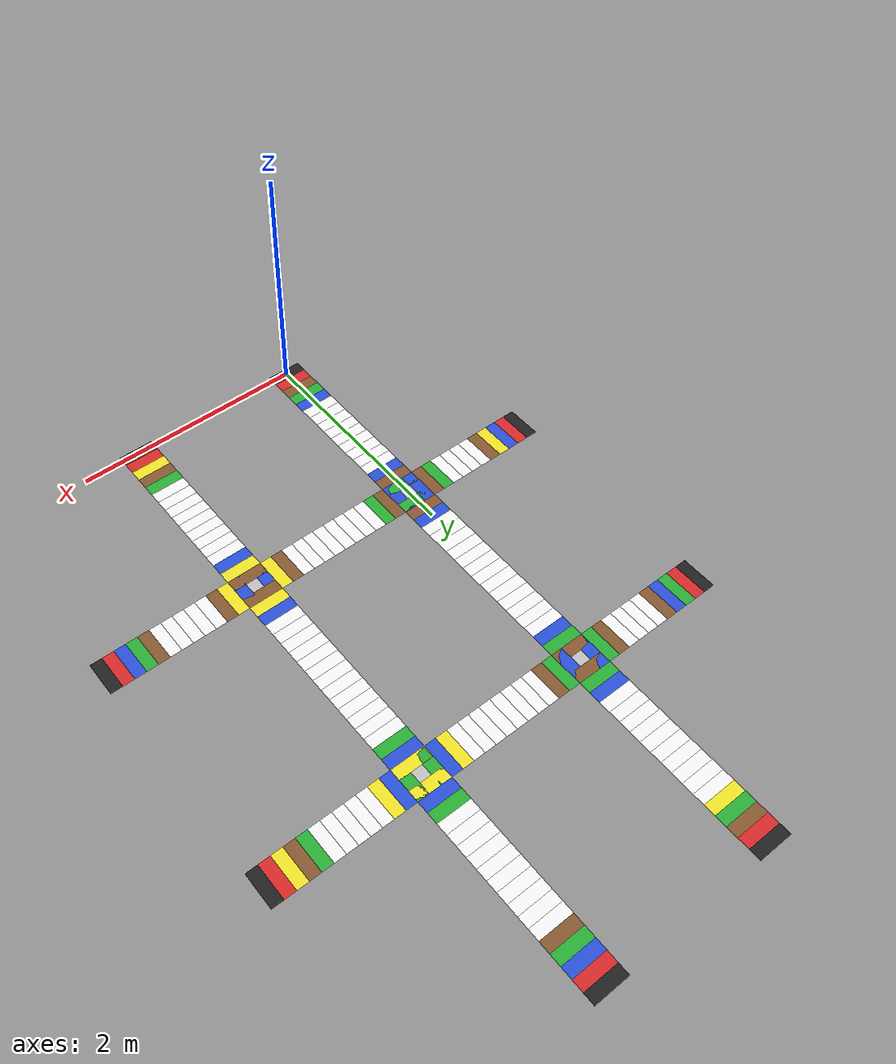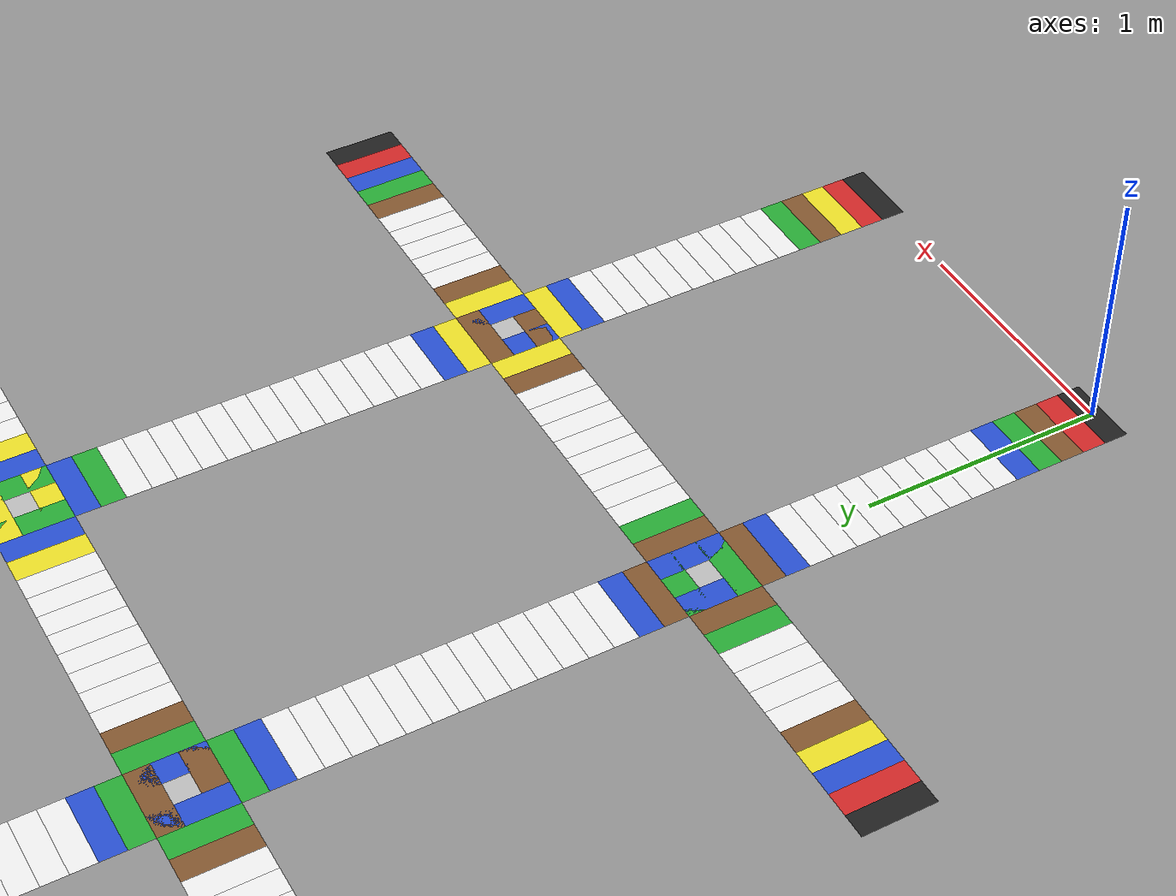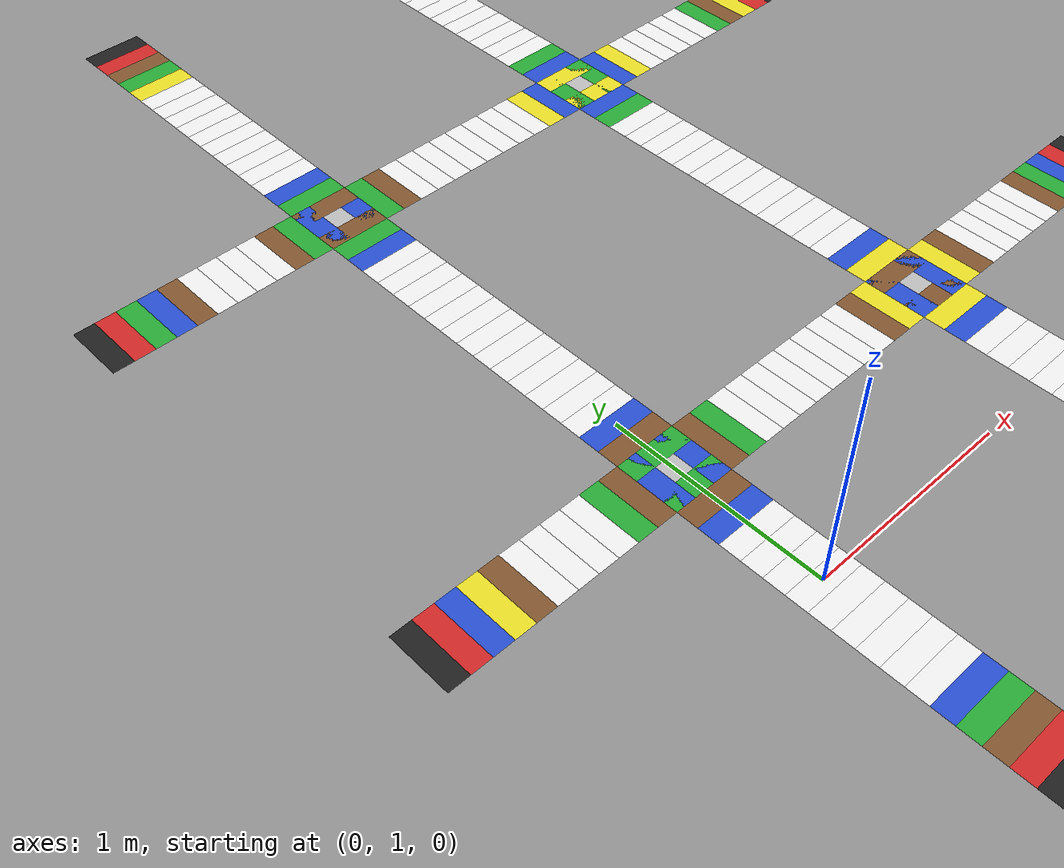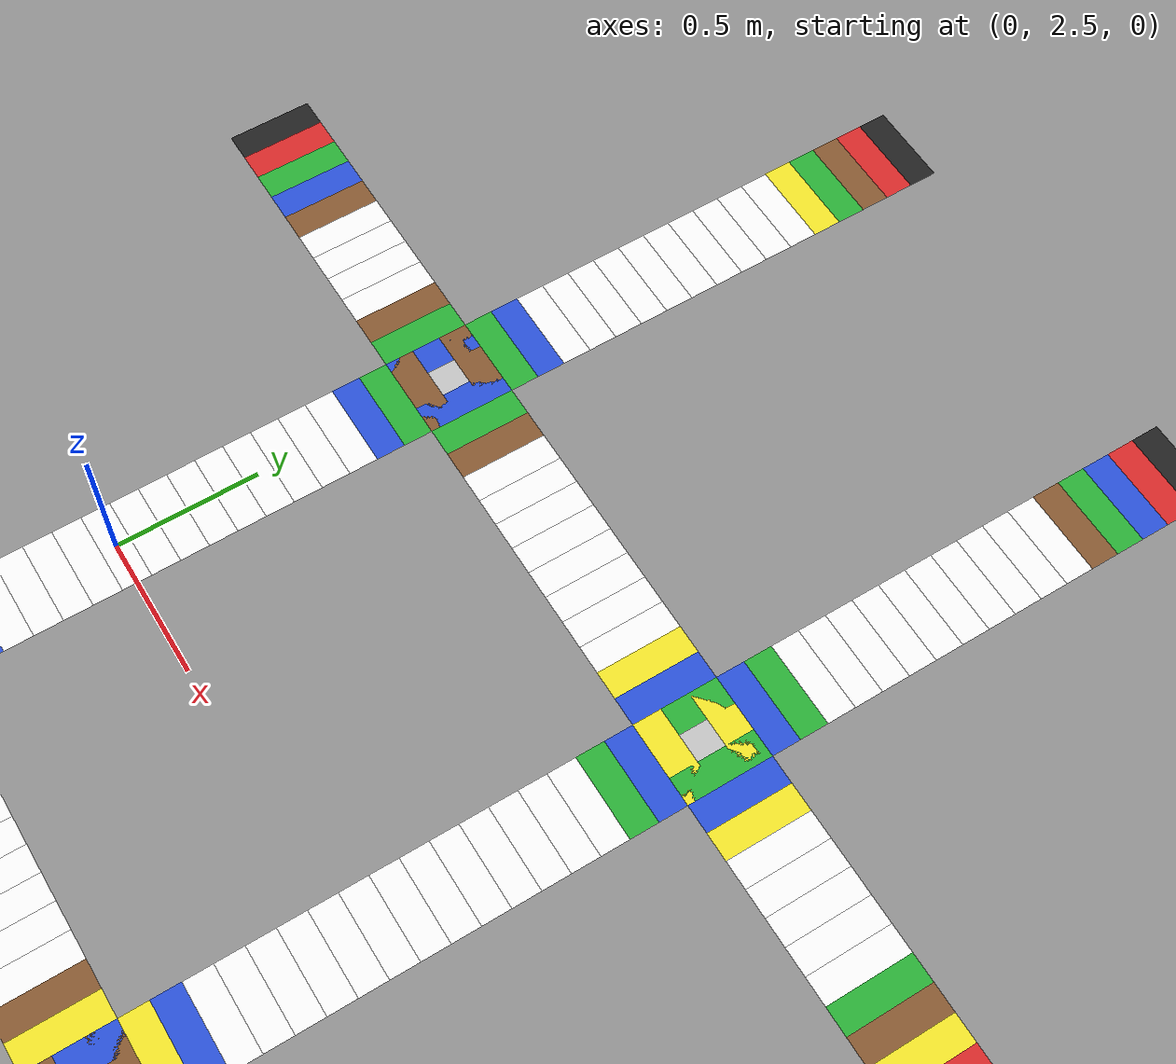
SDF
<sdf version="1.4">
 <world name="maskor_ev3_challenge">
  <light name="sun" type="directional">
   <pose>0 0 10 0 -0 0</pose>
   <diffuse>0.8 0.8 0.8 1</diffuse>
   <specular>0.2 0.2 0.2 1</specular>
   <attenuation>
    <range>1000</range>
    <constant>0.9</constant>
    <linear>0.01</linear>
    <quadratic>0.001</quadratic>
   </attenuation>
   <direction>-0.5 0.1 -0.9</direction>
  </light>
  <model name="tileAC3">
   <pose>0 0 0.001 0 -0 0</pose>
   <static>1</static>
   <link name="link">
    <pose>0 0 0.001 0 -0 0</pose>
    <visual name="visual">
     <geometry><mesh><uri>model://maskor_ev3_tile/meshes/ev3_tile.dae</uri><scale>5 5 5</scale></mesh></geometry>
     <material>
      <script>
       <uri>model://maskor_ev3_tile/materials/scripts</uri>
       <uri>model://maskor_ev3_tile/materials/textures</uri>
       <name>black</name>
      </script>
     </material>
    </visual>
    <velocity_decay><linear>0</linear><angular>0</angular></velocity_decay>
   </link>
  </model>
  <model name="tileAC21">
   <pose>0 1.8 0.001 0 -0 0</pose>
   <static>1</static>
   <link name="link">
    <pose>0 0 0.001 0 -0 0</pose>
    <visual name="visual">
     <geometry><mesh><uri>model://maskor_ev3_tile/meshes/ev3_tile.dae</uri><scale>5 5 5</scale></mesh></geometry>
     <material>
      <script>
       <uri>model://maskor_ev3_tile/materials/scripts</uri>
       <uri>model://maskor_ev3_tile/materials/textures</uri>
       <name>green</name>
      </script>
     </material>
    </visual>
    <velocity_decay><linear>0</linear><angular>0</angular></velocity_decay>
   </link>
  </model>
  <model name="tileAC4">
   <pose>0 0.1 0.001 0 -0 0</pose>
   <static>1</static>
   <link name="link">
    <pose>0 0 0.001 0 -0 0</pose>
    <visual name="visual">
     <geometry><mesh><uri>model://maskor_ev3_tile/meshes/ev3_tile.dae</uri><scale>5 5 5</scale></mesh></geometry>
     <material>
      <script>
       <uri>model://maskor_ev3_tile/materials/scripts</uri>
       <uri>model://maskor_ev3_tile/materials/textures</uri>
       <name>red</name>
      </script>
     </material>
    </visual>
    <velocity_decay><linear>0</linear><angular>0</angular></velocity_decay>
   </link>
  </model>
  <model name="tileAC5">
   <pose>0 0.2 0.001 0 -0 0</pose>
   <static>1</static>
   <link name="link">
    <pose>0 0 0.001 0 -0 0</pose>
    <visual name="visual">
     <geometry><mesh><uri>model://maskor_ev3_tile/meshes/ev3_tile.dae</uri><scale>5 5 5</scale></mesh></geometry>
     <material>
      <script>
       <uri>model://maskor_ev3_tile/materials/scripts</uri>
       <uri>model://maskor_ev3_tile/materials/textures</uri>
       <name>brown</name>
      </script>
     </material>
    </visual>
    <velocity_decay><linear>0</linear><angular>0</angular></velocity_decay>
   </link>
  </model>
  <model name="tileAC6">
   <pose>0 0.3 0.001 0 -0 0</pose>
   <static>1</static>
   <link name="link">
    <pose>0 0 0.001 0 -0 0</pose>
    <visual name="visual">
     <geometry><mesh><uri>model://maskor_ev3_tile/meshes/ev3_tile.dae</uri><scale>5 5 5</scale></mesh></geometry>
     <material>
      <script>
       <uri>model://maskor_ev3_tile/materials/scripts</uri>
       <uri>model://maskor_ev3_tile/materials/textures</uri>
       <name>green</name>
      </script>
     </material>
    </visual>
    <velocity_decay><linear>0</linear><angular>0</angular></velocity_decay>
   </link>
  </model>
  <model name="tileAC7">
   <pose>0 0.4 0.001 0 -0 0</pose>
   <static>1</static>
   <link name="link">
    <pose>0 0 0.001 0 -0 0</pose>
    <visual name="visual">
     <geometry><mesh><uri>model://maskor_ev3_tile/meshes/ev3_tile.dae</uri><scale>5 5 5</scale></mesh></geometry>
     <material>
      <script>
       <uri>model://maskor_ev3_tile/materials/scripts</uri>
       <uri>model://maskor_ev3_tile/materials/textures</uri>
       <name>blue</name>
      </script>
     </material>
    </visual>
    <velocity_decay><linear>0</linear><angular>0</angular></velocity_decay>
   </link>
  </model>
  <model name="tileAC8">
   <pose>0 0.5 0.001 0 -0 0</pose>
   <static>1</static>
   <link name="link">
    <pose>0 0 0.001 0 -0 0</pose>
    <visual name="visual">
     <geometry><mesh><uri>model://maskor_ev3_tile/meshes/ev3_tile.dae</uri><scale>5 5 5</scale></mesh></geometry>
     <material>
      <script>
       <uri>model://maskor_ev3_tile/materials/scripts</uri>
       <uri>model://maskor_ev3_tile/materials/textures</uri>
       <name>white</name>
      </script>
     </material>
    </visual>
    <velocity_decay><linear>0</linear><angular>0</angular></velocity_decay>
   </link>
  </model>
  <model name="tileAC9">
   <pose>0 0.6 0.001 0 -0 0</pose>
   <static>1</static>
   <link name="link">
    <pose>0 0 0.001 0 -0 0</pose>
    <visual name="visual">
     <geometry><mesh><uri>model://maskor_ev3_tile/meshes/ev3_tile.dae</uri><scale>5 5 5</scale></mesh></geometry>
     <material>
      <script>
       <uri>model://maskor_ev3_tile/materials/scripts</uri>
       <uri>model://maskor_ev3_tile/materials/textures</uri>
       <name>white</name>
      </script>
     </material>
    </visual>
    <velocity_decay><linear>0</linear><angular>0</angular></velocity_decay>
   </link>
  </model>
  <model name="tileAC10">
   <pose>0 0.7 0.001 0 -0 0</pose>
   <static>1</static>
   <link name="link">
    <pose>0 0 0.001 0 -0 0</pose>
    <visual name="visual">
     <geometry><mesh><uri>model://maskor_ev3_tile/meshes/ev3_tile.dae</uri><scale>5 5 5</scale></mesh></geometry>
     <material>
      <script>
       <uri>model://maskor_ev3_tile/materials/scripts</uri>
       <uri>model://maskor_ev3_tile/materials/textures</uri>
       <name>white</name>
      </script>
     </material>
    </visual>
    <velocity_decay><linear>0</linear><angular>0</angular></velocity_decay>
   </link>
  </model>
  <model name="tileAC11">
   <pose>0 0.8 0.001 0 -0 0</pose>
   <static>1</static>
   <link name="link">
    <pose>0 0 0.001 0 -0 0</pose>
    <visual name="visual">
     <geometry><mesh><uri>model://maskor_ev3_tile/meshes/ev3_tile.dae</uri><scale>5 5 5</scale></mesh></geometry>
     <material>
      <script>
       <uri>model://maskor_ev3_tile/materials/scripts</uri>
       <uri>model://maskor_ev3_tile/materials/textures</uri>
       <name>white</name>
      </script>
     </material>
    </visual>
    <velocity_decay><linear>0</linear><angular>0</angular></velocity_decay>
   </link>
  </model>
  <model name="tileAC12">
   <pose>0 0.9 0.001 0 -0 0</pose>
   <static>1</static>
   <link name="link">
    <pose>0 0 0.001 0 -0 0</pose>
    <visual name="visual">
     <geometry><mesh><uri>model://maskor_ev3_tile/meshes/ev3_tile.dae</uri><scale>5 5 5</scale></mesh></geometry>
     <material>
      <script>
       <uri>model://maskor_ev3_tile/materials/scripts</uri>
       <uri>model://maskor_ev3_tile/materials/textures</uri>
       <name>white</name>
      </script>
     </material>
    </visual>
    <velocity_decay><linear>0</linear><angular>0</angular></velocity_decay>
   </link>
  </model>
  <model name="tileAC13">
   <pose>0 1 0.001 0 -0 0</pose>
   <static>1</static>
   <link name="link">
    <pose>0 0 0.001 0 -0 0</pose>
    <visual name="visual">
     <geometry><mesh><uri>model://maskor_ev3_tile/meshes/ev3_tile.dae</uri><scale>5 5 5</scale></mesh></geometry>
     <material>
      <script>
       <uri>model://maskor_ev3_tile/materials/scripts</uri>
       <uri>model://maskor_ev3_tile/materials/textures</uri>
       <name>white</name>
      </script>
     </material>
    </visual>
    <velocity_decay><linear>0</linear><angular>0</angular></velocity_decay>
   </link>
  </model>
  <model name="tileAC14">
   <pose>0 1.1 0.001 0 -0 0</pose>
   <static>1</static>
   <link name="link">
    <pose>0 0 0.001 0 -0 0</pose>
    <visual name="visual">
     <geometry><mesh><uri>model://maskor_ev3_tile/meshes/ev3_tile.dae</uri><scale>5 5 5</scale></mesh></geometry>
     <material>
      <script>
       <uri>model://maskor_ev3_tile/materials/scripts</uri>
       <uri>model://maskor_ev3_tile/materials/textures</uri>
       <name>white</name>
      </script>
     </material>
    </visual>
    <velocity_decay><linear>0</linear><angular>0</angular></velocity_decay>
   </link>
  </model>
  <model name="tileAC15">
   <pose>0 1.2 0.001 0 -0 0</pose>
   <static>1</static>
   <link name="link">
    <pose>0 0 0.001 0 -0 0</pose>
    <visual name="visual">
     <geometry><mesh><uri>model://maskor_ev3_tile/meshes/ev3_tile.dae</uri><scale>5 5 5</scale></mesh></geometry>
     <material>
      <script>
       <uri>model://maskor_ev3_tile/materials/scripts</uri>
       <uri>model://maskor_ev3_tile/materials/textures</uri>
       <name>white</name>
      </script>
     </material>
    </visual>
    <velocity_decay><linear>0</linear><angular>0</angular></velocity_decay>
   </link>
  </model>
  <model name="tileAC16">
   <pose>0 1.3 0.001 0 -0 0</pose>
   <static>1</static>
   <link name="link">
    <pose>0 0 0.001 0 -0 0</pose>
    <visual name="visual">
     <geometry><mesh><uri>model://maskor_ev3_tile/meshes/ev3_tile.dae</uri><scale>5 5 5</scale></mesh></geometry>
     <material>
      <script>
       <uri>model://maskor_ev3_tile/materials/scripts</uri>
       <uri>model://maskor_ev3_tile/materials/textures</uri>
       <name>white</name>
      </script>
     </material>
    </visual>
    <velocity_decay><linear>0</linear><angular>0</angular></velocity_decay>
   </link>
  </model>
  <model name="tileAC17">
   <pose>0 1.4 0.001 0 -0 0</pose>
   <static>1</static>
   <link name="link">
    <pose>0 0 0.001 0 -0 0</pose>
    <visual name="visual">
     <geometry><mesh><uri>model://maskor_ev3_tile/meshes/ev3_tile.dae</uri><scale>5 5 5</scale></mesh></geometry>
     <material>
      <script>
       <uri>model://maskor_ev3_tile/materials/scripts</uri>
       <uri>model://maskor_ev3_tile/materials/textures</uri>
       <name>blue</name>
      </script>
     </material>
    </visual>
    <velocity_decay><linear>0</linear><angular>0</angular></velocity_decay>
   </link>
  </model>
  <model name="tileAC18">
   <pose>0 1.5 0.001 0 -0 0</pose>
   <static>1</static>
   <link name="link">
    <pose>0 0 0.001 0 -0 0</pose>
    <visual name="visual">
     <geometry><mesh><uri>model://maskor_ev3_tile/meshes/ev3_tile.dae</uri><scale>5 5 5</scale></mesh></geometry>
     <material>
      <script>
       <uri>model://maskor_ev3_tile/materials/scripts</uri>
       <uri>model://maskor_ev3_tile/materials/textures</uri>
       <name>brown</name>
      </script>
     </material>
    </visual>
    <velocity_decay><linear>0</linear><angular>0</angular></velocity_decay>
   </link>
  </model>
  <model name="tileAC19">
   <pose>0 1.6 0.001 0 -0 0</pose>
   <static>1</static>
   <link name="link">
    <pose>0 0 0.001 0 -0 0</pose>
    <visual name="visual">
     <geometry><mesh><uri>model://maskor_ev3_tile/meshes/ev3_tile.dae</uri><scale>5 5 5</scale></mesh></geometry>
     <material>
      <script>
       <uri>model://maskor_ev3_tile/materials/scripts</uri>
       <uri>model://maskor_ev3_tile/materials/textures</uri>
       <name>green</name>
      </script>
     </material>
    </visual>
    <velocity_decay><linear>0</linear><angular>0</angular></velocity_decay>
   </link>
  </model>
  <model name="tileAC20">
   <pose>0 1.7 0.002 0 -0 0</pose>
   <static>1</static>
   <link name="link">
    <visual name="visual">
     <geometry>
      <mesh><uri>model://maskor_ev3_tile_center/meshes/ev3_tile_center.dae</uri><scale>5 5 5</scale></mesh>
     </geometry>
     <material>
      <script>
       <uri>model://maskor_ev3_tile_center/materials/scripts</uri>
       <uri>model://maskor_ev3_tile_center/materials/textures</uri>
       <name>center</name>
      </script>
     </material>
    </visual>
    <velocity_decay><linear>0</linear><angular>0</angular></velocity_decay>
   </link>
  </model>
  <model name="tileAC22">
   <pose>0 1.9 0.001 0 -0 0</pose>
   <static>1</static>
   <link name="link">
    <pose>0 0 0.001 0 -0 0</pose>
    <visual name="visual">
     <geometry><mesh><uri>model://maskor_ev3_tile/meshes/ev3_tile.dae</uri><scale>5 5 5</scale></mesh></geometry>
     <material>
      <script>
       <uri>model://maskor_ev3_tile/materials/scripts</uri>
       <uri>model://maskor_ev3_tile/materials/textures</uri>
       <name>brown</name>
      </script>
     </material>
    </visual>
    <velocity_decay><linear>0</linear><angular>0</angular></velocity_decay>
   </link>
  </model>
  <model name="tileAC23">
   <pose>0 2 0.001 0 -0 0</pose>
   <static>1</static>
   <link name="link">
    <pose>0 0 0.001 0 -0 0</pose>
    <visual name="visual">
     <geometry><mesh><uri>model://maskor_ev3_tile/meshes/ev3_tile.dae</uri><scale>5 5 5</scale></mesh></geometry>
     <material>
      <script>
       <uri>model://maskor_ev3_tile/materials/scripts</uri>
       <uri>model://maskor_ev3_tile/materials/textures</uri>
       <name>blue</name>
      </script>
     </material>
    </visual>
    <velocity_decay><linear>0</linear><angular>0</angular></velocity_decay>
   </link>
  </model>
  <model name="tileAC24">
   <pose>0 2.1 0.001 0 -0 0</pose>
   <static>1</static>
   <link name="link">
    <pose>0 0 0.001 0 -0 0</pose>
    <visual name="visual">
     <geometry><mesh><uri>model://maskor_ev3_tile/meshes/ev3_tile.dae</uri><scale>5 5 5</scale></mesh></geometry>
     <material>
      <script>
       <uri>model://maskor_ev3_tile/materials/scripts</uri>
       <uri>model://maskor_ev3_tile/materials/textures</uri>
       <name>white</name>
      </script>
     </material>
    </visual>
    <velocity_decay><linear>0</linear><angular>0</angular></velocity_decay>
   </link>
  </model>
  <model name="tileAC25">
   <pose>0 2.2 0.001 0 -0 0</pose>
   <static>1</static>
   <link name="link">
    <pose>0 0 0.001 0 -0 0</pose>
    <visual name="visual">
     <geometry><mesh><uri>model://maskor_ev3_tile/meshes/ev3_tile.dae</uri><scale>5 5 5</scale></mesh></geometry>
     <material>
      <script>
       <uri>model://maskor_ev3_tile/materials/scripts</uri>
       <uri>model://maskor_ev3_tile/materials/textures</uri>
       <name>white</name>
      </script>
     </material>
    </visual>
    <velocity_decay><linear>0</linear><angular>0</angular></velocity_decay>
   </link>
  </model>
  <model name="tileAC26">
   <pose>0 2.3 0.001 0 -0 0</pose>
   <static>1</static>
   <link name="link">
    <pose>0 0 0.001 0 -0 0</pose>
    <visual name="visual">
     <geometry><mesh><uri>model://maskor_ev3_tile/meshes/ev3_tile.dae</uri><scale>5 5 5</scale></mesh></geometry>
     <material>
      <script>
       <uri>model://maskor_ev3_tile/materials/scripts</uri>
       <uri>model://maskor_ev3_tile/materials/textures</uri>
       <name>white</name>
      </script>
     </material>
    </visual>
    <velocity_decay><linear>0</linear><angular>0</angular></velocity_decay>
   </link>
  </model>
  <model name="tileAC27">
   <pose>0 2.4 0.001 0 -0 0</pose>
   <static>1</static>
   <link name="link">
    <pose>0 0 0.001 0 -0 0</pose>
    <visual name="visual">
     <geometry><mesh><uri>model://maskor_ev3_tile/meshes/ev3_tile.dae</uri><scale>5 5 5</scale></mesh></geometry>
     <material>
      <script>
       <uri>model://maskor_ev3_tile/materials/scripts</uri>
       <uri>model://maskor_ev3_tile/materials/textures</uri>
       <name>white</name>
      </script>
     </material>
    </visual>
    <velocity_decay><linear>0</linear><angular>0</angular></velocity_decay>
   </link>
  </model>
  <model name="tileAC34">
   <pose>0 3.1 0.001 0 -0 0</pose>
   <static>1</static>
   <link name="link">
    <pose>0 0 0.001 0 -0 0</pose>
    <visual name="visual">
     <geometry><mesh><uri>model://maskor_ev3_tile/meshes/ev3_tile.dae</uri><scale>5 5 5</scale></mesh></geometry>
     <material>
      <script>
       <uri>model://maskor_ev3_tile/materials/scripts</uri>
       <uri>model://maskor_ev3_tile/materials/textures</uri>
       <name>white</name>
      </script>
     </material>
    </visual>
    <velocity_decay><linear>0</linear><angular>0</angular></velocity_decay>
   </link>
  </model>
  <model name="tileAC28">
   <pose>0 2.5 0.001 0 -0 0</pose>
   <static>1</static>
   <link name="link">
    <pose>0 0 0.001 0 -0 0</pose>
    <visual name="visual">
     <geometry><mesh><uri>model://maskor_ev3_tile/meshes/ev3_tile.dae</uri><scale>5 5 5</scale></mesh></geometry>
     <material>
      <script>
       <uri>model://maskor_ev3_tile/materials/scripts</uri>
       <uri>model://maskor_ev3_tile/materials/textures</uri>
       <name>white</name>
      </script>
     </material>
    </visual>
    <velocity_decay><linear>0</linear><angular>0</angular></velocity_decay>
   </link>
  </model>
  <model name="tileAC29">
   <pose>0 2.6 0.001 0 -0 0</pose>
   <static>1</static>
   <link name="link">
    <pose>0 0 0.001 0 -0 0</pose>
    <visual name="visual">
     <geometry><mesh><uri>model://maskor_ev3_tile/meshes/ev3_tile.dae</uri><scale>5 5 5</scale></mesh></geometry>
     <material>
      <script>
       <uri>model://maskor_ev3_tile/materials/scripts</uri>
       <uri>model://maskor_ev3_tile/materials/textures</uri>
       <name>white</name>
      </script>
     </material>
    </visual>
    <velocity_decay><linear>0</linear><angular>0</angular></velocity_decay>
   </link>
  </model>
  <model name="tileAC30">
   <pose>0 2.7 0.001 0 -0 0</pose>
   <static>1</static>
   <link name="link">
    <pose>0 0 0.001 0 -0 0</pose>
    <visual name="visual">
     <geometry><mesh><uri>model://maskor_ev3_tile/meshes/ev3_tile.dae</uri><scale>5 5 5</scale></mesh></geometry>
     <material>
      <script>
       <uri>model://maskor_ev3_tile/materials/scripts</uri>
       <uri>model://maskor_ev3_tile/materials/textures</uri>
       <name>white</name>
      </script>
     </material>
    </visual>
    <velocity_decay><linear>0</linear><angular>0</angular></velocity_decay>
   </link>
  </model>
  <model name="tileAC31">
   <pose>0 2.8 0.001 0 -0 0</pose>
   <static>1</static>
   <link name="link">
    <pose>0 0 0.001 0 -0 0</pose>
    <visual name="visual">
     <geometry><mesh><uri>model://maskor_ev3_tile/meshes/ev3_tile.dae</uri><scale>5 5 5</scale></mesh></geometry>
     <material>
      <script>
       <uri>model://maskor_ev3_tile/materials/scripts</uri>
       <uri>model://maskor_ev3_tile/materials/textures</uri>
       <name>white</name>
      </script>
     </material>
    </visual>
    <velocity_decay><linear>0</linear><angular>0</angular></velocity_decay>
   </link>
  </model>
  <model name="tileAC32">
   <pose>0 2.9 0.001 0 -0 0</pose>
   <static>1</static>
   <link name="link">
    <pose>0 0 0.001 0 -0 0</pose>
    <visual name="visual">
     <geometry><mesh><uri>model://maskor_ev3_tile/meshes/ev3_tile.dae</uri><scale>5 5 5</scale></mesh></geometry>
     <material>
      <script>
       <uri>model://maskor_ev3_tile/materials/scripts</uri>
       <uri>model://maskor_ev3_tile/materials/textures</uri>
       <name>white</name>
      </script>
     </material>
    </visual>
    <velocity_decay><linear>0</linear><angular>0</angular></velocity_decay>
   </link>
  </model>
  <model name="tileAC33">
   <pose>0 3 0.001 0 -0 0</pose>
   <static>1</static>
   <link name="link">
    <pose>0 0 0.001 0 -0 0</pose>
    <visual name="visual">
     <geometry><mesh><uri>model://maskor_ev3_tile/meshes/ev3_tile.dae</uri><scale>5 5 5</scale></mesh></geometry>
     <material>
      <script>
       <uri>model://maskor_ev3_tile/materials/scripts</uri>
       <uri>model://maskor_ev3_tile/materials/textures</uri>
       <name>white</name>
      </script>
     </material>
    </visual>
    <velocity_decay><linear>0</linear><angular>0</angular></velocity_decay>
   </link>
  </model>
  <model name="tileAC35">
   <pose>0 3.2 0.001 0 -0 0</pose>
   <static>1</static>
   <link name="link">
    <pose>0 0 0.001 0 -0 0</pose>
    <visual name="visual">
     <geometry><mesh><uri>model://maskor_ev3_tile/meshes/ev3_tile.dae</uri><scale>5 5 5</scale></mesh></geometry>
     <material>
      <script>
       <uri>model://maskor_ev3_tile/materials/scripts</uri>
       <uri>model://maskor_ev3_tile/materials/textures</uri>
       <name>white</name>
      </script>
     </material>
    </visual>
    <velocity_decay><linear>0</linear><angular>0</angular></velocity_decay>
   </link>
  </model>
  <model name="tileAC36">
   <pose>0 3.3 0.001 0 -0 0</pose>
   <static>1</static>
   <link name="link">
    <pose>0 0 0.001 0 -0 0</pose>
    <visual name="visual">
     <geometry><mesh><uri>model://maskor_ev3_tile/meshes/ev3_tile.dae</uri><scale>5 5 5</scale></mesh></geometry>
     <material>
      <script>
       <uri>model://maskor_ev3_tile/materials/scripts</uri>
       <uri>model://maskor_ev3_tile/materials/textures</uri>
       <name>white</name>
      </script>
     </material>
    </visual>
    <velocity_decay><linear>0</linear><angular>0</angular></velocity_decay>
   </link>
  </model>
  <model name="tileAC37">
   <pose>0 3.4 0.001 0 -0 0</pose>
   <static>1</static>
   <link name="link">
    <pose>0 0 0.001 0 -0 0</pose>
    <visual name="visual">
     <geometry><mesh><uri>model://maskor_ev3_tile/meshes/ev3_tile.dae</uri><scale>5 5 5</scale></mesh></geometry>
     <material>
      <script>
       <uri>model://maskor_ev3_tile/materials/scripts</uri>
       <uri>model://maskor_ev3_tile/materials/textures</uri>
       <name>blue</name>
      </script>
     </material>
    </visual>
    <velocity_decay><linear>0</linear><angular>0</angular></velocity_decay>
   </link>
  </model>
  <model name="tileAC38">
   <pose>0 3.5 0.001 0 -0 0</pose>
   <static>1</static>
   <link name="link">
    <pose>0 0 0.001 0 -0 0</pose>
    <visual name="visual">
     <geometry><mesh><uri>model://maskor_ev3_tile/meshes/ev3_tile.dae</uri><scale>5 5 5</scale></mesh></geometry>
     <material>
      <script>
       <uri>model://maskor_ev3_tile/materials/scripts</uri>
       <uri>model://maskor_ev3_tile/materials/textures</uri>
       <name>green</name>
      </script>
     </material>
    </visual>
    <velocity_decay><linear>0</linear><angular>0</angular></velocity_decay>
   </link>
  </model>
  <model name="tileAC39">
   <pose>0 3.6 0.001 0 -0 0</pose>
   <static>1</static>
   <link name="link">
    <pose>0 0 0.001 0 -0 0</pose>
    <visual name="visual">
     <geometry><mesh><uri>model://maskor_ev3_tile/meshes/ev3_tile.dae</uri><scale>5 5 5</scale></mesh></geometry>
     <material>
      <script>
       <uri>model://maskor_ev3_tile/materials/scripts</uri>
       <uri>model://maskor_ev3_tile/materials/textures</uri>
       <name>brown</name>
      </script>
     </material>
    </visual>
    <velocity_decay><linear>0</linear><angular>0</angular></velocity_decay>
   </link>
  </model>
  <model name="tileAC40">
   <pose>0 3.7 0.002 0 -0 0</pose>
   <static>1</static>
   <link name="link">
    <visual name="visual">
     <geometry>
      <mesh><uri>model://maskor_ev3_tile_center/meshes/ev3_tile_center.dae</uri><scale>5 5 5</scale></mesh>
     </geometry>
     <material>
      <script>
       <uri>model://maskor_ev3_tile_center/materials/scripts</uri>
       <uri>model://maskor_ev3_tile_center/materials/textures</uri>
       <name>center</name>
      </script>
     </material>
    </visual>
    <velocity_decay><linear>0</linear><angular>0</angular></velocity_decay>
   </link>
  </model>
  <model name="tileAC41">
   <pose>0 3.8 0.001 0 -0 0</pose>
   <static>1</static>
   <link name="link">
    <pose>0 0 0.001 0 -0 0</pose>
    <visual name="visual">
     <geometry><mesh><uri>model://maskor_ev3_tile/meshes/ev3_tile.dae</uri><scale>5 5 5</scale></mesh></geometry>
     <material>
      <script>
       <uri>model://maskor_ev3_tile/materials/scripts</uri>
       <uri>model://maskor_ev3_tile/materials/textures</uri>
       <name>brown</name>
      </script>
     </material>
    </visual>
    <velocity_decay><linear>0</linear><angular>0</angular></velocity_decay>
   </link>
  </model>
  <model name="tileAC42">
   <pose>0 3.9 0.001 0 -0 0</pose>
   <static>1</static>
   <link name="link">
    <pose>0 0 0.001 0 -0 0</pose>
    <visual name="visual">
     <geometry><mesh><uri>model://maskor_ev3_tile/meshes/ev3_tile.dae</uri><scale>5 5 5</scale></mesh></geometry>
     <material>
      <script>
       <uri>model://maskor_ev3_tile/materials/scripts</uri>
       <uri>model://maskor_ev3_tile/materials/textures</uri>
       <name>green</name>
      </script>
     </material>
    </visual>
    <velocity_decay><linear>0</linear><angular>0</angular></velocity_decay>
   </link>
  </model>
  <model name="tileAC43">
   <pose>0 4 0.001 0 -0 0</pose>
   <static>1</static>
   <link name="link">
    <pose>0 0 0.001 0 -0 0</pose>
    <visual name="visual">
     <geometry><mesh><uri>model://maskor_ev3_tile/meshes/ev3_tile.dae</uri><scale>5 5 5</scale></mesh></geometry>
     <material>
      <script>
       <uri>model://maskor_ev3_tile/materials/scripts</uri>
       <uri>model://maskor_ev3_tile/materials/textures</uri>
       <name>blue</name>
      </script>
     </material>
    </visual>
    <velocity_decay><linear>0</linear><angular>0</angular></velocity_decay>
   </link>
  </model>
  <model name="tileAC44">
   <pose>0 4.1 0.001 0 -0 0</pose>
   <static>1</static>
   <link name="link">
    <pose>0 0 0.001 0 -0 0</pose>
    <visual name="visual">
     <geometry><mesh><uri>model://maskor_ev3_tile/meshes/ev3_tile.dae</uri><scale>5 5 5</scale></mesh></geometry>
     <material>
      <script>
       <uri>model://maskor_ev3_tile/materials/scripts</uri>
       <uri>model://maskor_ev3_tile/materials/textures</uri>
       <name>white</name>
      </script>
     </material>
    </visual>
    <velocity_decay><linear>0</linear><angular>0</angular></velocity_decay>
   </link>
  </model>
  <model name="tileAC45">
   <pose>0 4.2 0.001 0 -0 0</pose>
   <static>1</static>
   <link name="link">
    <pose>0 0 0.001 0 -0 0</pose>
    <visual name="visual">
     <geometry><mesh><uri>model://maskor_ev3_tile/meshes/ev3_tile.dae</uri><scale>5 5 5</scale></mesh></geometry>
     <material>
      <script>
       <uri>model://maskor_ev3_tile/materials/scripts</uri>
       <uri>model://maskor_ev3_tile/materials/textures</uri>
       <name>white</name>
      </script>
     </material>
    </visual>
    <velocity_decay><linear>0</linear><angular>0</angular></velocity_decay>
   </link>
  </model>
  <model name="tileAC46">
   <pose>0 4.3 0.001 0 -0 0</pose>
   <static>1</static>
   <link name="link">
    <pose>0 0 0.001 0 -0 0</pose>
    <visual name="visual">
     <geometry><mesh><uri>model://maskor_ev3_tile/meshes/ev3_tile.dae</uri><scale>5 5 5</scale></mesh></geometry>
     <material>
      <script>
       <uri>model://maskor_ev3_tile/materials/scripts</uri>
       <uri>model://maskor_ev3_tile/materials/textures</uri>
       <name>white</name>
      </script>
     </material>
    </visual>
    <velocity_decay><linear>0</linear><angular>0</angular></velocity_decay>
   </link>
  </model>
  <model name="tileAC53">
   <pose>0 5 0.001 0 -0 0</pose>
   <static>1</static>
   <link name="link">
    <pose>0 0 0.001 0 -0 0</pose>
    <visual name="visual">
     <geometry><mesh><uri>model://maskor_ev3_tile/meshes/ev3_tile.dae</uri><scale>5 5 5</scale></mesh></geometry>
     <material>
      <script>
       <uri>model://maskor_ev3_tile/materials/scripts</uri>
       <uri>model://maskor_ev3_tile/materials/textures</uri>
       <name>white</name>
      </script>
     </material>
    </visual>
    <velocity_decay><linear>0</linear><angular>0</angular></velocity_decay>
   </link>
  </model>
  <model name="tileAC47">
   <pose>0 4.4 0.001 0 -0 0</pose>
   <static>1</static>
   <link name="link">
    <pose>0 0 0.001 0 -0 0</pose>
    <visual name="visual">
     <geometry><mesh><uri>model://maskor_ev3_tile/meshes/ev3_tile.dae</uri><scale>5 5 5</scale></mesh></geometry>
     <material>
      <script>
       <uri>model://maskor_ev3_tile/materials/scripts</uri>
       <uri>model://maskor_ev3_tile/materials/textures</uri>
       <name>white</name>
      </script>
     </material>
    </visual>
    <velocity_decay><linear>0</linear><angular>0</angular></velocity_decay>
   </link>
  </model>
  <model name="tileAC48">
   <pose>0 4.5 0.001 0 -0 0</pose>
   <static>1</static>
   <link name="link">
    <pose>0 0 0.001 0 -0 0</pose>
    <visual name="visual">
     <geometry><mesh><uri>model://maskor_ev3_tile/meshes/ev3_tile.dae</uri><scale>5 5 5</scale></mesh></geometry>
     <material>
      <script>
       <uri>model://maskor_ev3_tile/materials/scripts</uri>
       <uri>model://maskor_ev3_tile/materials/textures</uri>
       <name>white</name>
      </script>
     </material>
    </visual>
    <velocity_decay><linear>0</linear><angular>0</angular></velocity_decay>
   </link>
  </model>
  <model name="tileAC49">
   <pose>0 4.6 0.001 0 -0 0</pose>
   <static>1</static>
   <link name="link">
    <pose>0 0 0.001 0 -0 0</pose>
    <visual name="visual">
     <geometry><mesh><uri>model://maskor_ev3_tile/meshes/ev3_tile.dae</uri><scale>5 5 5</scale></mesh></geometry>
     <material>
      <script>
       <uri>model://maskor_ev3_tile/materials/scripts</uri>
       <uri>model://maskor_ev3_tile/materials/textures</uri>
       <name>white</name>
      </script>
     </material>
    </visual>
    <velocity_decay><linear>0</linear><angular>0</angular></velocity_decay>
   </link>
  </model>
  <model name="tileAC50">
   <pose>0 4.7 0.001 0 -0 0</pose>
   <static>1</static>
   <link name="link">
    <pose>0 0 0.001 0 -0 0</pose>
    <visual name="visual">
     <geometry><mesh><uri>model://maskor_ev3_tile/meshes/ev3_tile.dae</uri><scale>5 5 5</scale></mesh></geometry>
     <material>
      <script>
       <uri>model://maskor_ev3_tile/materials/scripts</uri>
       <uri>model://maskor_ev3_tile/materials/textures</uri>
       <name>white</name>
      </script>
     </material>
    </visual>
    <velocity_decay><linear>0</linear><angular>0</angular></velocity_decay>
   </link>
  </model>
  <model name="tileAC51">
   <pose>0 4.8 0.001 0 -0 0</pose>
   <static>1</static>
   <link name="link">
    <pose>0 0 0.001 0 -0 0</pose>
    <visual name="visual">
     <geometry><mesh><uri>model://maskor_ev3_tile/meshes/ev3_tile.dae</uri><scale>5 5 5</scale></mesh></geometry>
     <material>
      <script>
       <uri>model://maskor_ev3_tile/materials/scripts</uri>
       <uri>model://maskor_ev3_tile/materials/textures</uri>
       <name>white</name>
      </script>
     </material>
    </visual>
    <velocity_decay><linear>0</linear><angular>0</angular></velocity_decay>
   </link>
  </model>
  <model name="tileAC52">
   <pose>0 4.9 0.001 0 -0 0</pose>
   <static>1</static>
   <link name="link">
    <pose>0 0 0.001 0 -0 0</pose>
    <visual name="visual">
     <geometry><mesh><uri>model://maskor_ev3_tile/meshes/ev3_tile.dae</uri><scale>5 5 5</scale></mesh></geometry>
     <material>
      <script>
       <uri>model://maskor_ev3_tile/materials/scripts</uri>
       <uri>model://maskor_ev3_tile/materials/textures</uri>
       <name>white</name>
      </script>
     </material>
    </visual>
    <velocity_decay><linear>0</linear><angular>0</angular></velocity_decay>
   </link>
  </model>
  <model name="tileAC54">
   <pose>0 5.1 0.001 0 -0 0</pose>
   <static>1</static>
   <link name="link">
    <pose>0 0 0.001 0 -0 0</pose>
    <visual name="visual">
     <geometry><mesh><uri>model://maskor_ev3_tile/meshes/ev3_tile.dae</uri><scale>5 5 5</scale></mesh></geometry>
     <material>
      <script>
       <uri>model://maskor_ev3_tile/materials/scripts</uri>
       <uri>model://maskor_ev3_tile/materials/textures</uri>
       <name>yellow</name>
      </script>
     </material>
    </visual>
    <velocity_decay><linear>0</linear><angular>0</angular></velocity_decay>
   </link>
  </model>
  <model name="tileAC55">
   <pose>0 5.2 0.001 0 -0 0</pose>
   <static>1</static>
   <link name="link">
    <pose>0 0 0.001 0 -0 0</pose>
    <visual name="visual">
     <geometry><mesh><uri>model://maskor_ev3_tile/meshes/ev3_tile.dae</uri><scale>5 5 5</scale></mesh></geometry>
     <material>
      <script>
       <uri>model://maskor_ev3_tile/materials/scripts</uri>
       <uri>model://maskor_ev3_tile/materials/textures</uri>
       <name>green</name>
      </script>
     </material>
    </visual>
    <velocity_decay><linear>0</linear><angular>0</angular></velocity_decay>
   </link>
  </model>
  <model name="tileAC56">
   <pose>0 5.3 0.001 0 -0 0</pose>
   <static>1</static>
   <link name="link">
    <pose>0 0 0.001 0 -0 0</pose>
    <visual name="visual">
     <geometry><mesh><uri>model://maskor_ev3_tile/meshes/ev3_tile.dae</uri><scale>5 5 5</scale></mesh></geometry>
     <material>
      <script>
       <uri>model://maskor_ev3_tile/materials/scripts</uri>
       <uri>model://maskor_ev3_tile/materials/textures</uri>
       <name>brown</name>
      </script>
     </material>
    </visual>
    <velocity_decay><linear>0</linear><angular>0</angular></velocity_decay>
   </link>
  </model>
  <model name="tileAC57">
   <pose>0 5.4 0.001 0 -0 0</pose>
   <static>1</static>
   <link name="link">
    <pose>0 0 0.001 0 -0 0</pose>
    <visual name="visual">
     <geometry><mesh><uri>model://maskor_ev3_tile/meshes/ev3_tile.dae</uri><scale>5 5 5</scale></mesh></geometry>
     <material>
      <script>
       <uri>model://maskor_ev3_tile/materials/scripts</uri>
       <uri>model://maskor_ev3_tile/materials/textures</uri>
       <name>red</name>
      </script>
     </material>
    </visual>
    <velocity_decay><linear>0</linear><angular>0</angular></velocity_decay>
   </link>
  </model>
  <model name="tileAC58">
   <pose>0 5.5 0.001 0 -0 0</pose>
   <static>1</static>
   <link name="link">
    <pose>0 0 0.001 0 -0 0</pose>
    <visual name="visual">
     <geometry><mesh><uri>model://maskor_ev3_tile/meshes/ev3_tile.dae</uri><scale>5 5 5</scale></mesh></geometry>
     <material>
      <script>
       <uri>model://maskor_ev3_tile/materials/scripts</uri>
       <uri>model://maskor_ev3_tile/materials/textures</uri>
       <name>black</name>
      </script>
     </material>
    </visual>
    <velocity_decay><linear>0</linear><angular>0</angular></velocity_decay>
   </link>
  </model>
  <model name="tileBD3">
   <pose>1.5 0 0.001 0 -0 0</pose>
   <static>1</static>
   <link name="link">
    <pose>0 0 0.001 0 -0 0</pose>
    <visual name="visual">
     <geometry><mesh><uri>model://maskor_ev3_tile/meshes/ev3_tile.dae</uri><scale>5 5 5</scale></mesh></geometry>
     <material>
      <script>
       <uri>model://maskor_ev3_tile/materials/scripts</uri>
       <uri>model://maskor_ev3_tile/materials/textures</uri>
       <name>black</name>
      </script>
     </material>
    </visual>
    <velocity_decay><linear>0</linear><angular>0</angular></velocity_decay>
   </link>
  </model>
  <model name="tileBD4">
   <pose>1.5 0.1 0.001 0 -0 0</pose>
   <static>1</static>
   <link name="link">
    <pose>0 0 0.001 0 -0 0</pose>
    <visual name="visual">
     <geometry><mesh><uri>model://maskor_ev3_tile/meshes/ev3_tile.dae</uri><scale>5 5 5</scale></mesh></geometry>
     <material>
      <script>
       <uri>model://maskor_ev3_tile/materials/scripts</uri>
       <uri>model://maskor_ev3_tile/materials/textures</uri>
       <name>red</name>
      </script>
     </material>
    </visual>
    <velocity_decay><linear>0</linear><angular>0</angular></velocity_decay>
   </link>
  </model>
  <model name="tileBD5">
   <pose>1.5 0.2 0.001 0 -0 0</pose>
   <static>1</static>
   <link name="link">
    <pose>0 0 0.001 0 -0 0</pose>
    <visual name="visual">
     <geometry><mesh><uri>model://maskor_ev3_tile/meshes/ev3_tile.dae</uri><scale>5 5 5</scale></mesh></geometry>
     <material>
      <script>
       <uri>model://maskor_ev3_tile/materials/scripts</uri>
       <uri>model://maskor_ev3_tile/materials/textures</uri>
       <name>yellow</name>
      </script>
     </material>
    </visual>
    <velocity_decay><linear>0</linear><angular>0</angular></velocity_decay>
   </link>
  </model>
  <model name="tileBD6">
   <pose>1.5 0.3 0.001 0 -0 0</pose>
   <static>1</static>
   <link name="link">
    <pose>0 0 0.001 0 -0 0</pose>
    <visual name="visual">
     <geometry><mesh><uri>model://maskor_ev3_tile/meshes/ev3_tile.dae</uri><scale>5 5 5</scale></mesh></geometry>
     <material>
      <script>
       <uri>model://maskor_ev3_tile/materials/scripts</uri>
       <uri>model://maskor_ev3_tile/materials/textures</uri>
       <name>brown</name>
      </script>
     </material>
    </visual>
    <velocity_decay><linear>0</linear><angular>0</angular></velocity_decay>
   </link>
  </model>
  <model name="tileBD7">
   <pose>1.5 0.4 0.001 0 -0 0</pose>
   <static>1</static>
   <link name="link">
    <pose>0 0 0.001 0 -0 0</pose>
    <visual name="visual">
     <geometry><mesh><uri>model://maskor_ev3_tile/meshes/ev3_tile.dae</uri><scale>5 5 5</scale></mesh></geometry>
     <material>
      <script>
       <uri>model://maskor_ev3_tile/materials/scripts</uri>
       <uri>model://maskor_ev3_tile/materials/textures</uri>
       <name>green</name>
      </script>
     </material>
    </visual>
    <velocity_decay><linear>0</linear><angular>0</angular></velocity_decay>
   </link>
  </model>
  <model name="tileBD8">
   <pose>1.5 0.5 0.001 0 -0 0</pose>
   <static>1</static>
   <link name="link">
    <pose>0 0 0.001 0 -0 0</pose>
    <visual name="visual">
     <geometry><mesh><uri>model://maskor_ev3_tile/meshes/ev3_tile.dae</uri><scale>5 5 5</scale></mesh></geometry>
     <material>
      <script>
       <uri>model://maskor_ev3_tile/materials/scripts</uri>
       <uri>model://maskor_ev3_tile/materials/textures</uri>
       <name>white</name>
      </script>
     </material>
    </visual>
    <velocity_decay><linear>0</linear><angular>0</angular></velocity_decay>
   </link>
  </model>
  <model name="tileBD9">
   <pose>1.5 0.6 0.001 0 -0 0</pose>
   <static>1</static>
   <link name="link">
    <pose>0 0 0.001 0 -0 0</pose>
    <visual name="visual">
     <geometry><mesh><uri>model://maskor_ev3_tile/meshes/ev3_tile.dae</uri><scale>5 5 5</scale></mesh></geometry>
     <material>
      <script>
       <uri>model://maskor_ev3_tile/materials/scripts</uri>
       <uri>model://maskor_ev3_tile/materials/textures</uri>
       <name>white</name>
      </script>
     </material>
    </visual>
    <velocity_decay><linear>0</linear><angular>0</angular></velocity_decay>
   </link>
  </model>
  <model name="tileBD10">
   <pose>1.5 0.7 0.001 0 -0 0</pose>
   <static>1</static>
   <link name="link">
    <pose>0 0 0.001 0 -0 0</pose>
    <visual name="visual">
     <geometry><mesh><uri>model://maskor_ev3_tile/meshes/ev3_tile.dae</uri><scale>5 5 5</scale></mesh></geometry>
     <material>
      <script>
       <uri>model://maskor_ev3_tile/materials/scripts</uri>
       <uri>model://maskor_ev3_tile/materials/textures</uri>
       <name>white</name>
      </script>
     </material>
    </visual>
    <velocity_decay><linear>0</linear><angular>0</angular></velocity_decay>
   </link>
  </model>
  <model name="tileBD11">
   <pose>1.5 0.8 0.001 0 -0 0</pose>
   <static>1</static>
   <link name="link">
    <pose>0 0 0.001 0 -0 0</pose>
    <visual name="visual">
     <geometry><mesh><uri>model://maskor_ev3_tile/meshes/ev3_tile.dae</uri><scale>5 5 5</scale></mesh></geometry>
     <material>
      <script>
       <uri>model://maskor_ev3_tile/materials/scripts</uri>
       <uri>model://maskor_ev3_tile/materials/textures</uri>
       <name>white</name>
      </script>
     </material>
    </visual>
    <velocity_decay><linear>0</linear><angular>0</angular></velocity_decay>
   </link>
  </model>
  <model name="tileBD12">
   <pose>1.5 0.9 0.001 0 -0 0</pose>
   <static>1</static>
   <link name="link">
    <pose>0 0 0.001 0 -0 0</pose>
    <visual name="visual">
     <geometry><mesh><uri>model://maskor_ev3_tile/meshes/ev3_tile.dae</uri><scale>5 5 5</scale></mesh></geometry>
     <material>
      <script>
       <uri>model://maskor_ev3_tile/materials/scripts</uri>
       <uri>model://maskor_ev3_tile/materials/textures</uri>
       <name>white</name>
      </script>
     </material>
    </visual>
    <velocity_decay><linear>0</linear><angular>0</angular></velocity_decay>
   </link>
  </model>
  <model name="tileBD13">
   <pose>1.5 1 0.001 0 -0 0</pose>
   <static>1</static>
   <link name="link">
    <pose>0 0 0.001 0 -0 0</pose>
    <visual name="visual">
     <geometry><mesh><uri>model://maskor_ev3_tile/meshes/ev3_tile.dae</uri><scale>5 5 5</scale></mesh></geometry>
     <material>
      <script>
       <uri>model://maskor_ev3_tile/materials/scripts</uri>
       <uri>model://maskor_ev3_tile/materials/textures</uri>
       <name>white</name>
      </script>
     </material>
    </visual>
    <velocity_decay><linear>0</linear><angular>0</angular></velocity_decay>
   </link>
  </model>
  <model name="tileBD14">
   <pose>1.5 1.1 0.001 0 -0 0</pose>
   <static>1</static>
   <link name="link">
    <pose>0 0 0.001 0 -0 0</pose>
    <visual name="visual">
     <geometry><mesh><uri>model://maskor_ev3_tile/meshes/ev3_tile.dae</uri><scale>5 5 5</scale></mesh></geometry>
     <material>
      <script>
       <uri>model://maskor_ev3_tile/materials/scripts</uri>
       <uri>model://maskor_ev3_tile/materials/textures</uri>
       <name>white</name>
      </script>
     </material>
    </visual>
    <velocity_decay><linear>0</linear><angular>0</angular></velocity_decay>
   </link>
  </model>
  <model name="tileBD15">
   <pose>1.5 1.2 0.001 0 -0 0</pose>
   <static>1</static>
   <link name="link">
    <pose>0 0 0.001 0 -0 0</pose>
    <visual name="visual">
     <geometry><mesh><uri>model://maskor_ev3_tile/meshes/ev3_tile.dae</uri><scale>5 5 5</scale></mesh></geometry>
     <material>
      <script>
       <uri>model://maskor_ev3_tile/materials/scripts</uri>
       <uri>model://maskor_ev3_tile/materials/textures</uri>
       <name>white</name>
      </script>
     </material>
    </visual>
    <velocity_decay><linear>0</linear><angular>0</angular></velocity_decay>
   </link>
  </model>
  <model name="tileBD16">
   <pose>1.5 1.3 0.001 0 -0 0</pose>
   <static>1</static>
   <link name="link">
    <pose>0 0 0.001 0 -0 0</pose>
    <visual name="visual">
     <geometry><mesh><uri>model://maskor_ev3_tile/meshes/ev3_tile.dae</uri><scale>5 5 5</scale></mesh></geometry>
     <material>
      <script>
       <uri>model://maskor_ev3_tile/materials/scripts</uri>
       <uri>model://maskor_ev3_tile/materials/textures</uri>
       <name>white</name>
      </script>
     </material>
    </visual>
    <velocity_decay><linear>0</linear><angular>0</angular></velocity_decay>
   </link>
  </model>
  <model name="tileBD22">
   <pose>1.5 1.9 0.001 0 -0 0</pose>
   <static>1</static>
   <link name="link">
    <pose>0 0 0.001 0 -0 0</pose>
    <visual name="visual">
     <geometry><mesh><uri>model://maskor_ev3_tile/meshes/ev3_tile.dae</uri><scale>5 5 5</scale></mesh></geometry>
     <material>
      <script>
       <uri>model://maskor_ev3_tile/materials/scripts</uri>
       <uri>model://maskor_ev3_tile/materials/textures</uri>
       <name>yellow</name>
      </script>
     </material>
    </visual>
    <velocity_decay><linear>0</linear><angular>0</angular></velocity_decay>
   </link>
  </model>
  <model name="tileBD17">
   <pose>1.5 1.4 0.001 0 -0 0</pose>
   <static>1</static>
   <link name="link">
    <pose>0 0 0.001 0 -0 0</pose>
    <visual name="visual">
     <geometry><mesh><uri>model://maskor_ev3_tile/meshes/ev3_tile.dae</uri><scale>5 5 5</scale></mesh></geometry>
     <material>
      <script>
       <uri>model://maskor_ev3_tile/materials/scripts</uri>
       <uri>model://maskor_ev3_tile/materials/textures</uri>
       <name>blue</name>
      </script>
     </material>
    </visual>
    <velocity_decay><linear>0</linear><angular>0</angular></velocity_decay>
   </link>
  </model>
  <model name="tileBD18">
   <pose>1.5 1.5 0.001 0 -0 0</pose>
   <static>1</static>
   <link name="link">
    <pose>0 0 0.001 0 -0 0</pose>
    <visual name="visual">
     <geometry><mesh><uri>model://maskor_ev3_tile/meshes/ev3_tile.dae</uri><scale>5 5 5</scale></mesh></geometry>
     <material>
      <script>
       <uri>model://maskor_ev3_tile/materials/scripts</uri>
       <uri>model://maskor_ev3_tile/materials/textures</uri>
       <name>yellow</name>
      </script>
     </material>
    </visual>
    <velocity_decay><linear>0</linear><angular>0</angular></velocity_decay>
   </link>
  </model>
  <model name="tileBD19">
   <pose>1.5 1.6 0.001 0 -0 0</pose>
   <static>1</static>
   <link name="link">
    <pose>0 0 0.001 0 -0 0</pose>
    <visual name="visual">
     <geometry><mesh><uri>model://maskor_ev3_tile/meshes/ev3_tile.dae</uri><scale>5 5 5</scale></mesh></geometry>
     <material>
      <script>
       <uri>model://maskor_ev3_tile/materials/scripts</uri>
       <uri>model://maskor_ev3_tile/materials/textures</uri>
       <name>brown</name>
      </script>
     </material>
    </visual>
    <velocity_decay><linear>0</linear><angular>0</angular></velocity_decay>
   </link>
  </model>
  <model name="tileBD20">
   <pose>1.5 1.7 0.002 0 -0 0</pose>
   <static>1</static>
   <link name="link">
    <visual name="visual">
     <geometry>
      <mesh><uri>model://maskor_ev3_tile_center/meshes/ev3_tile_center.dae</uri><scale>5 5 5</scale></mesh>
     </geometry>
     <material>
      <script>
       <uri>model://maskor_ev3_tile_center/materials/scripts</uri>
       <uri>model://maskor_ev3_tile_center/materials/textures</uri>
       <name>center</name>
      </script>
     </material>
    </visual>
    <velocity_decay><linear>0</linear><angular>0</angular></velocity_decay>
   </link>
  </model>
  <model name="tileBD21">
   <pose>1.5 1.8 0.001 0 -0 0</pose>
   <static>1</static>
   <link name="link">
    <pose>0 0 0.001 0 -0 0</pose>
    <visual name="visual">
     <geometry><mesh><uri>model://maskor_ev3_tile/meshes/ev3_tile.dae</uri><scale>5 5 5</scale></mesh></geometry>
     <material>
      <script>
       <uri>model://maskor_ev3_tile/materials/scripts</uri>
       <uri>model://maskor_ev3_tile/materials/textures</uri>
       <name>brown</name>
      </script>
     </material>
    </visual>
    <velocity_decay><linear>0</linear><angular>0</angular></velocity_decay>
   </link>
  </model>
  <model name="tileBD28">
   <pose>1.5 2.5 0.001 0 -0 0</pose>
   <static>1</static>
   <link name="link">
    <pose>0 0 0.001 0 -0 0</pose>
    <visual name="visual">
     <geometry><mesh><uri>model://maskor_ev3_tile/meshes/ev3_tile.dae</uri><scale>5 5 5</scale></mesh></geometry>
     <material>
      <script>
       <uri>model://maskor_ev3_tile/materials/scripts</uri>
       <uri>model://maskor_ev3_tile/materials/textures</uri>
       <name>white</name>
      </script>
     </material>
    </visual>
    <velocity_decay><linear>0</linear><angular>0</angular></velocity_decay>
   </link>
  </model>
  <model name="tileBD23">
   <pose>1.5 2 0.001 0 -0 0</pose>
   <static>1</static>
   <link name="link">
    <pose>0 0 0.001 0 -0 0</pose>
    <visual name="visual">
     <geometry><mesh><uri>model://maskor_ev3_tile/meshes/ev3_tile.dae</uri><scale>5 5 5</scale></mesh></geometry>
     <material>
      <script>
       <uri>model://maskor_ev3_tile/materials/scripts</uri>
       <uri>model://maskor_ev3_tile/materials/textures</uri>
       <name>blue</name>
      </script>
     </material>
    </visual>
    <velocity_decay><linear>0</linear><angular>0</angular></velocity_decay>
   </link>
  </model>
  <model name="tileBD24">
   <pose>1.5 2.1 0.001 0 -0 0</pose>
   <static>1</static>
   <link name="link">
    <pose>0 0 0.001 0 -0 0</pose>
    <visual name="visual">
     <geometry><mesh><uri>model://maskor_ev3_tile/meshes/ev3_tile.dae</uri><scale>5 5 5</scale></mesh></geometry>
     <material>
      <script>
       <uri>model://maskor_ev3_tile/materials/scripts</uri>
       <uri>model://maskor_ev3_tile/materials/textures</uri>
       <name>white</name>
      </script>
     </material>
    </visual>
    <velocity_decay><linear>0</linear><angular>0</angular></velocity_decay>
   </link>
  </model>
  <model name="tileBD25">
   <pose>1.5 2.2 0.001 0 -0 0</pose>
   <static>1</static>
   <link name="link">
    <pose>0 0 0.001 0 -0 0</pose>
    <visual name="visual">
     <geometry><mesh><uri>model://maskor_ev3_tile/meshes/ev3_tile.dae</uri><scale>5 5 5</scale></mesh></geometry>
     <material>
      <script>
       <uri>model://maskor_ev3_tile/materials/scripts</uri>
       <uri>model://maskor_ev3_tile/materials/textures</uri>
       <name>white</name>
      </script>
     </material>
    </visual>
    <velocity_decay><linear>0</linear><angular>0</angular></velocity_decay>
   </link>
  </model>
  <model name="tileBD26">
   <pose>1.5 2.3 0.001 0 -0 0</pose>
   <static>1</static>
   <link name="link">
    <pose>0 0 0.001 0 -0 0</pose>
    <visual name="visual">
     <geometry><mesh><uri>model://maskor_ev3_tile/meshes/ev3_tile.dae</uri><scale>5 5 5</scale></mesh></geometry>
     <material>
      <script>
       <uri>model://maskor_ev3_tile/materials/scripts</uri>
       <uri>model://maskor_ev3_tile/materials/textures</uri>
       <name>white</name>
      </script>
     </material>
    </visual>
    <velocity_decay><linear>0</linear><angular>0</angular></velocity_decay>
   </link>
  </model>
  <model name="tileBD27">
   <pose>1.5 2.4 0.001 0 -0 0</pose>
   <static>1</static>
   <link name="link">
    <pose>0 0 0.001 0 -0 0</pose>
    <visual name="visual">
     <geometry><mesh><uri>model://maskor_ev3_tile/meshes/ev3_tile.dae</uri><scale>5 5 5</scale></mesh></geometry>
     <material>
      <script>
       <uri>model://maskor_ev3_tile/materials/scripts</uri>
       <uri>model://maskor_ev3_tile/materials/textures</uri>
       <name>white</name>
      </script>
     </material>
    </visual>
    <velocity_decay><linear>0</linear><angular>0</angular></velocity_decay>
   </link>
  </model>
  <model name="tileBD29">
   <pose>1.5 2.6 0.001 0 -0 0</pose>
   <static>1</static>
   <link name="link">
    <pose>0 0 0.001 0 -0 0</pose>
    <visual name="visual">
     <geometry><mesh><uri>model://maskor_ev3_tile/meshes/ev3_tile.dae</uri><scale>5 5 5</scale></mesh></geometry>
     <material>
      <script>
       <uri>model://maskor_ev3_tile/materials/scripts</uri>
       <uri>model://maskor_ev3_tile/materials/textures</uri>
       <name>white</name>
      </script>
     </material>
    </visual>
    <velocity_decay><linear>0</linear><angular>0</angular></velocity_decay>
   </link>
  </model>
  <model name="tileBD30">
   <pose>1.5 2.7 0.001 0 -0 0</pose>
   <static>1</static>
   <link name="link">
    <pose>0 0 0.001 0 -0 0</pose>
    <visual name="visual">
     <geometry><mesh><uri>model://maskor_ev3_tile/meshes/ev3_tile.dae</uri><scale>5 5 5</scale></mesh></geometry>
     <material>
      <script>
       <uri>model://maskor_ev3_tile/materials/scripts</uri>
       <uri>model://maskor_ev3_tile/materials/textures</uri>
       <name>white</name>
      </script>
     </material>
    </visual>
    <velocity_decay><linear>0</linear><angular>0</angular></velocity_decay>
   </link>
  </model>
  <model name="tileBD31">
   <pose>1.5 2.8 0.001 0 -0 0</pose>
   <static>1</static>
   <link name="link">
    <pose>0 0 0.001 0 -0 0</pose>
    <visual name="visual">
     <geometry><mesh><uri>model://maskor_ev3_tile/meshes/ev3_tile.dae</uri><scale>5 5 5</scale></mesh></geometry>
     <material>
      <script>
       <uri>model://maskor_ev3_tile/materials/scripts</uri>
       <uri>model://maskor_ev3_tile/materials/textures</uri>
       <name>white</name>
      </script>
     </material>
    </visual>
    <velocity_decay><linear>0</linear><angular>0</angular></velocity_decay>
   </link>
  </model>
  <model name="tileBD32">
   <pose>1.5 2.9 0.001 0 -0 0</pose>
   <static>1</static>
   <link name="link">
    <pose>0 0 0.001 0 -0 0</pose>
    <visual name="visual">
     <geometry><mesh><uri>model://maskor_ev3_tile/meshes/ev3_tile.dae</uri><scale>5 5 5</scale></mesh></geometry>
     <material>
      <script>
       <uri>model://maskor_ev3_tile/materials/scripts</uri>
       <uri>model://maskor_ev3_tile/materials/textures</uri>
       <name>white</name>
      </script>
     </material>
    </visual>
    <velocity_decay><linear>0</linear><angular>0</angular></velocity_decay>
   </link>
  </model>
  <model name="tileBD33">
   <pose>1.5 3 0.001 0 -0 0</pose>
   <static>1</static>
   <link name="link">
    <pose>0 0 0.001 0 -0 0</pose>
    <visual name="visual">
     <geometry><mesh><uri>model://maskor_ev3_tile/meshes/ev3_tile.dae</uri><scale>5 5 5</scale></mesh></geometry>
     <material>
      <script>
       <uri>model://maskor_ev3_tile/materials/scripts</uri>
       <uri>model://maskor_ev3_tile/materials/textures</uri>
       <name>white</name>
      </script>
     </material>
    </visual>
    <velocity_decay><linear>0</linear><angular>0</angular></velocity_decay>
   </link>
  </model>
  <model name="tileBD34">
   <pose>1.5 3.1 0.001 0 -0 0</pose>
   <static>1</static>
   <link name="link">
    <pose>0 0 0.001 0 -0 0</pose>
    <visual name="visual">
     <geometry><mesh><uri>model://maskor_ev3_tile/meshes/ev3_tile.dae</uri><scale>5 5 5</scale></mesh></geometry>
     <material>
      <script>
       <uri>model://maskor_ev3_tile/materials/scripts</uri>
       <uri>model://maskor_ev3_tile/materials/textures</uri>
       <name>white</name>
      </script>
     </material>
    </visual>
    <velocity_decay><linear>0</linear><angular>0</angular></velocity_decay>
   </link>
  </model>
  <model name="tileBD35">
   <pose>1.5 3.2 0.001 0 -0 0</pose>
   <static>1</static>
   <link name="link">
    <pose>0 0 0.001 0 -0 0</pose>
    <visual name="visual">
     <geometry><mesh><uri>model://maskor_ev3_tile/meshes/ev3_tile.dae</uri><scale>5 5 5</scale></mesh></geometry>
     <material>
      <script>
       <uri>model://maskor_ev3_tile/materials/scripts</uri>
       <uri>model://maskor_ev3_tile/materials/textures</uri>
       <name>white</name>
      </script>
     </material>
    </visual>
    <velocity_decay><linear>0</linear><angular>0</angular></velocity_decay>
   </link>
  </model>
  <model name="tileBD36">
   <pose>1.5 3.3 0.001 0 -0 0</pose>
   <static>1</static>
   <link name="link">
    <pose>0 0 0.001 0 -0 0</pose>
    <visual name="visual">
     <geometry><mesh><uri>model://maskor_ev3_tile/meshes/ev3_tile.dae</uri><scale>5 5 5</scale></mesh></geometry>
     <material>
      <script>
       <uri>model://maskor_ev3_tile/materials/scripts</uri>
       <uri>model://maskor_ev3_tile/materials/textures</uri>
       <name>white</name>
      </script>
     </material>
    </visual>
    <velocity_decay><linear>0</linear><angular>0</angular></velocity_decay>
   </link>
  </model>
  <model name="tileBD37">
   <pose>1.5 3.4 0.001 0 -0 0</pose>
   <static>1</static>
   <link name="link">
    <pose>0 0 0.001 0 -0 0</pose>
    <visual name="visual">
     <geometry><mesh><uri>model://maskor_ev3_tile/meshes/ev3_tile.dae</uri><scale>5 5 5</scale></mesh></geometry>
     <material>
      <script>
       <uri>model://maskor_ev3_tile/materials/scripts</uri>
       <uri>model://maskor_ev3_tile/materials/textures</uri>
       <name>green</name>
      </script>
     </material>
    </visual>
    <velocity_decay><linear>0</linear><angular>0</angular></velocity_decay>
   </link>
  </model>
  <model name="tileBD38">
   <pose>1.5 3.5 0.001 0 -0 0</pose>
   <static>1</static>
   <link name="link">
    <pose>0 0 0.001 0 -0 0</pose>
    <visual name="visual">
     <geometry><mesh><uri>model://maskor_ev3_tile/meshes/ev3_tile.dae</uri><scale>5 5 5</scale></mesh></geometry>
     <material>
      <script>
       <uri>model://maskor_ev3_tile/materials/scripts</uri>
       <uri>model://maskor_ev3_tile/materials/textures</uri>
       <name>blue</name>
      </script>
     </material>
    </visual>
    <velocity_decay><linear>0</linear><angular>0</angular></velocity_decay>
   </link>
  </model>
  <model name="tileBD39">
   <pose>1.5 3.6 0.001 0 -0 0</pose>
   <static>1</static>
   <link name="link">
    <pose>0 0 0.001 0 -0 0</pose>
    <visual name="visual">
     <geometry><mesh><uri>model://maskor_ev3_tile/meshes/ev3_tile.dae</uri><scale>5 5 5</scale></mesh></geometry>
     <material>
      <script>
       <uri>model://maskor_ev3_tile/materials/scripts</uri>
       <uri>model://maskor_ev3_tile/materials/textures</uri>
       <name>yellow</name>
      </script>
     </material>
    </visual>
    <velocity_decay><linear>0</linear><angular>0</angular></velocity_decay>
   </link>
  </model>
  <model name="tileBD40">
   <pose>1.5 3.7 0.002 0 -0 0</pose>
   <static>1</static>
   <link name="link">
    <visual name="visual">
     <geometry>
      <mesh><uri>model://maskor_ev3_tile_center/meshes/ev3_tile_center.dae</uri><scale>5 5 5</scale></mesh>
     </geometry>
     <material>
      <script>
       <uri>model://maskor_ev3_tile_center/materials/scripts</uri>
       <uri>model://maskor_ev3_tile_center/materials/textures</uri>
       <name>center</name>
      </script>
     </material>
    </visual>
    <velocity_decay><linear>0</linear><angular>0</angular></velocity_decay>
   </link>
  </model>
  <model name="tileBD41">
   <pose>1.5 3.8 0.001 0 -0 0</pose>
   <static>1</static>
   <link name="link">
    <pose>0 0 0.001 0 -0 0</pose>
    <visual name="visual">
     <geometry><mesh><uri>model://maskor_ev3_tile/meshes/ev3_tile.dae</uri><scale>5 5 5</scale></mesh></geometry>
     <material>
      <script>
       <uri>model://maskor_ev3_tile/materials/scripts</uri>
       <uri>model://maskor_ev3_tile/materials/textures</uri>
       <name>yellow</name>
      </script>
     </material>
    </visual>
    <velocity_decay><linear>0</linear><angular>0</angular></velocity_decay>
   </link>
  </model>
  <model name="tileBD42">
   <pose>1.5 3.9 0.001 0 -0 0</pose>
   <static>1</static>
   <link name="link">
    <pose>0 0 0.001 0 -0 0</pose>
    <visual name="visual">
     <geometry><mesh><uri>model://maskor_ev3_tile/meshes/ev3_tile.dae</uri><scale>5 5 5</scale></mesh></geometry>
     <material>
      <script>
       <uri>model://maskor_ev3_tile/materials/scripts</uri>
       <uri>model://maskor_ev3_tile/materials/textures</uri>
       <name>blue</name>
      </script>
     </material>
    </visual>
    <velocity_decay><linear>0</linear><angular>0</angular></velocity_decay>
   </link>
  </model>
  <model name="tileBD43">
   <pose>1.5 4 0.001 0 -0 0</pose>
   <static>1</static>
   <link name="link">
    <pose>0 0 0.001 0 -0 0</pose>
    <visual name="visual">
     <geometry><mesh><uri>model://maskor_ev3_tile/meshes/ev3_tile.dae</uri><scale>5 5 5</scale></mesh></geometry>
     <material>
      <script>
       <uri>model://maskor_ev3_tile/materials/scripts</uri>
       <uri>model://maskor_ev3_tile/materials/textures</uri>
       <name>green</name>
      </script>
     </material>
    </visual>
    <velocity_decay><linear>0</linear><angular>0</angular></velocity_decay>
   </link>
  </model>
  <model name="tileBD44">
   <pose>1.5 4.1 0.001 0 -0 0</pose>
   <static>1</static>
   <link name="link">
    <pose>0 0 0.001 0 -0 0</pose>
    <visual name="visual">
     <geometry><mesh><uri>model://maskor_ev3_tile/meshes/ev3_tile.dae</uri><scale>5 5 5</scale></mesh></geometry>
     <material>
      <script>
       <uri>model://maskor_ev3_tile/materials/scripts</uri>
       <uri>model://maskor_ev3_tile/materials/textures</uri>
       <name>white</name>
      </script>
     </material>
    </visual>
    <velocity_decay><linear>0</linear><angular>0</angular></velocity_decay>
   </link>
  </model>
  <model name="tileBD45">
   <pose>1.5 4.2 0.001 0 -0 0</pose>
   <static>1</static>
   <link name="link">
    <pose>0 0 0.001 0 -0 0</pose>
    <visual name="visual">
     <geometry><mesh><uri>model://maskor_ev3_tile/meshes/ev3_tile.dae</uri><scale>5 5 5</scale></mesh></geometry>
     <material>
      <script>
       <uri>model://maskor_ev3_tile/materials/scripts</uri>
       <uri>model://maskor_ev3_tile/materials/textures</uri>
       <name>white</name>
      </script>
     </material>
    </visual>
    <velocity_decay><linear>0</linear><angular>0</angular></velocity_decay>
   </link>
  </model>
  <model name="tileBD46">
   <pose>1.5 4.3 0.001 0 -0 0</pose>
   <static>1</static>
   <link name="link">
    <pose>0 0 0.001 0 -0 0</pose>
    <visual name="visual">
     <geometry><mesh><uri>model://maskor_ev3_tile/meshes/ev3_tile.dae</uri><scale>5 5 5</scale></mesh></geometry>
     <material>
      <script>
       <uri>model://maskor_ev3_tile/materials/scripts</uri>
       <uri>model://maskor_ev3_tile/materials/textures</uri>
       <name>white</name>
      </script>
     </material>
    </visual>
    <velocity_decay><linear>0</linear><angular>0</angular></velocity_decay>
   </link>
  </model>
  <model name="tileBD47">
   <pose>1.5 4.4 0.001 0 -0 0</pose>
   <static>1</static>
   <link name="link">
    <pose>0 0 0.001 0 -0 0</pose>
    <visual name="visual">
     <geometry><mesh><uri>model://maskor_ev3_tile/meshes/ev3_tile.dae</uri><scale>5 5 5</scale></mesh></geometry>
     <material>
      <script>
       <uri>model://maskor_ev3_tile/materials/scripts</uri>
       <uri>model://maskor_ev3_tile/materials/textures</uri>
       <name>white</name>
      </script>
     </material>
    </visual>
    <velocity_decay><linear>0</linear><angular>0</angular></velocity_decay>
   </link>
  </model>
  <model name="tileBD48">
   <pose>1.5 4.5 0.001 0 -0 0</pose>
   <static>1</static>
   <link name="link">
    <pose>0 0 0.001 0 -0 0</pose>
    <visual name="visual">
     <geometry><mesh><uri>model://maskor_ev3_tile/meshes/ev3_tile.dae</uri><scale>5 5 5</scale></mesh></geometry>
     <material>
      <script>
       <uri>model://maskor_ev3_tile/materials/scripts</uri>
       <uri>model://maskor_ev3_tile/materials/textures</uri>
       <name>white</name>
      </script>
     </material>
    </visual>
    <velocity_decay><linear>0</linear><angular>0</angular></velocity_decay>
   </link>
  </model>
  <model name="tileBD49">
   <pose>1.5 4.6 0.001 0 -0 0</pose>
   <static>1</static>
   <link name="link">
    <pose>0 0 0.001 0 -0 0</pose>
    <visual name="visual">
     <geometry><mesh><uri>model://maskor_ev3_tile/meshes/ev3_tile.dae</uri><scale>5 5 5</scale></mesh></geometry>
     <material>
      <script>
       <uri>model://maskor_ev3_tile/materials/scripts</uri>
       <uri>model://maskor_ev3_tile/materials/textures</uri>
       <name>white</name>
      </script>
     </material>
    </visual>
    <velocity_decay><linear>0</linear><angular>0</angular></velocity_decay>
   </link>
  </model>
  <model name="tileBD50">
   <pose>1.5 4.7 0.001 0 -0 0</pose>
   <static>1</static>
   <link name="link">
    <pose>0 0 0.001 0 -0 0</pose>
    <visual name="visual">
     <geometry><mesh><uri>model://maskor_ev3_tile/meshes/ev3_tile.dae</uri><scale>5 5 5</scale></mesh></geometry>
     <material>
      <script>
       <uri>model://maskor_ev3_tile/materials/scripts</uri>
       <uri>model://maskor_ev3_tile/materials/textures</uri>
       <name>white</name>
      </script>
     </material>
    </visual>
    <velocity_decay><linear>0</linear><angular>0</angular></velocity_decay>
   </link>
  </model>
  <model name="tileBD51">
   <pose>1.5 4.8 0.001 0 -0 0</pose>
   <static>1</static>
   <link name="link">
    <pose>0 0 0.001 0 -0 0</pose>
    <visual name="visual">
     <geometry><mesh><uri>model://maskor_ev3_tile/meshes/ev3_tile.dae</uri><scale>5 5 5</scale></mesh></geometry>
     <material>
      <script>
       <uri>model://maskor_ev3_tile/materials/scripts</uri>
       <uri>model://maskor_ev3_tile/materials/textures</uri>
       <name>white</name>
      </script>
     </material>
    </visual>
    <velocity_decay><linear>0</linear><angular>0</angular></velocity_decay>
   </link>
  </model>
  <model name="tileBD52">
   <pose>1.5 4.9 0.001 0 -0 0</pose>
   <static>1</static>
   <link name="link">
    <pose>0 0 0.001 0 -0 0</pose>
    <visual name="visual">
     <geometry><mesh><uri>model://maskor_ev3_tile/meshes/ev3_tile.dae</uri><scale>5 5 5</scale></mesh></geometry>
     <material>
      <script>
       <uri>model://maskor_ev3_tile/materials/scripts</uri>
       <uri>model://maskor_ev3_tile/materials/textures</uri>
       <name>white</name>
      </script>
     </material>
    </visual>
    <velocity_decay><linear>0</linear><angular>0</angular></velocity_decay>
   </link>
  </model>
  <model name="tileEF3">
   <pose>-1.2 1.7 0.001 0 -0 1.5708</pose>
   <static>1</static>
   <link name="link">
    <pose>0 0 0.001 0 -0 0</pose>
    <visual name="visual">
     <geometry><mesh><uri>model://maskor_ev3_tile/meshes/ev3_tile.dae</uri><scale>5 5 5</scale></mesh></geometry>
     <material>
      <script>
       <uri>model://maskor_ev3_tile/materials/scripts</uri>
       <uri>model://maskor_ev3_tile/materials/textures</uri>
       <name>black</name>
      </script>
     </material>
    </visual>
    <velocity_decay><linear>0</linear><angular>0</angular></velocity_decay>
   </link>
  </model>
  <model name="tileBD53">
   <pose>1.5 5 0.001 0 -0 0</pose>
   <static>1</static>
   <link name="link">
    <pose>0 0 0.001 0 -0 0</pose>
    <visual name="visual">
     <geometry><mesh><uri>model://maskor_ev3_tile/meshes/ev3_tile.dae</uri><scale>5 5 5</scale></mesh></geometry>
     <material>
      <script>
       <uri>model://maskor_ev3_tile/materials/scripts</uri>
       <uri>model://maskor_ev3_tile/materials/textures</uri>
       <name>white</name>
      </script>
     </material>
    </visual>
    <velocity_decay><linear>0</linear><angular>0</angular></velocity_decay>
   </link>
  </model>
  <model name="tileBD54">
   <pose>1.5 5.1 0.001 0 -0 0</pose>
   <static>1</static>
   <link name="link">
    <pose>0 0 0.001 0 -0 0</pose>
    <visual name="visual">
     <geometry><mesh><uri>model://maskor_ev3_tile/meshes/ev3_tile.dae</uri><scale>5 5 5</scale></mesh></geometry>
     <material>
      <script>
       <uri>model://maskor_ev3_tile/materials/scripts</uri>
       <uri>model://maskor_ev3_tile/materials/textures</uri>
       <name>brown</name>
      </script>
     </material>
    </visual>
    <velocity_decay><linear>0</linear><angular>0</angular></velocity_decay>
   </link>
  </model>
  <model name="tileBD55">
   <pose>1.5 5.2 0.001 0 -0 0</pose>
   <static>1</static>
   <link name="link">
    <pose>0 0 0.001 0 -0 0</pose>
    <visual name="visual">
     <geometry><mesh><uri>model://maskor_ev3_tile/meshes/ev3_tile.dae</uri><scale>5 5 5</scale></mesh></geometry>
     <material>
      <script>
       <uri>model://maskor_ev3_tile/materials/scripts</uri>
       <uri>model://maskor_ev3_tile/materials/textures</uri>
       <name>green</name>
      </script>
     </material>
    </visual>
    <velocity_decay><linear>0</linear><angular>0</angular></velocity_decay>
   </link>
  </model>
  <model name="tileBD56">
   <pose>1.5 5.3 0.001 0 -0 0</pose>
   <static>1</static>
   <link name="link">
    <pose>0 0 0.001 0 -0 0</pose>
    <visual name="visual">
     <geometry><mesh><uri>model://maskor_ev3_tile/meshes/ev3_tile.dae</uri><scale>5 5 5</scale></mesh></geometry>
     <material>
      <script>
       <uri>model://maskor_ev3_tile/materials/scripts</uri>
       <uri>model://maskor_ev3_tile/materials/textures</uri>
       <name>blue</name>
      </script>
     </material>
    </visual>
    <velocity_decay><linear>0</linear><angular>0</angular></velocity_decay>
   </link>
  </model>
  <model name="tileBD57">
   <pose>1.5 5.4 0.001 0 -0 0</pose>
   <static>1</static>
   <link name="link">
    <pose>0 0 0.001 0 -0 0</pose>
    <visual name="visual">
     <geometry><mesh><uri>model://maskor_ev3_tile/meshes/ev3_tile.dae</uri><scale>5 5 5</scale></mesh></geometry>
     <material>
      <script>
       <uri>model://maskor_ev3_tile/materials/scripts</uri>
       <uri>model://maskor_ev3_tile/materials/textures</uri>
       <name>red</name>
      </script>
     </material>
    </visual>
    <velocity_decay><linear>0</linear><angular>0</angular></velocity_decay>
   </link>
  </model>
  <model name="tileBD58">
   <pose>1.5 5.5 0.001 0 -0 0</pose>
   <static>1</static>
   <link name="link">
    <pose>0 0 0.001 0 -0 0</pose>
    <visual name="visual">
     <geometry><mesh><uri>model://maskor_ev3_tile/meshes/ev3_tile.dae</uri><scale>5 5 5</scale></mesh></geometry>
     <material>
      <script>
       <uri>model://maskor_ev3_tile/materials/scripts</uri>
       <uri>model://maskor_ev3_tile/materials/textures</uri>
       <name>black</name>
      </script>
     </material>
    </visual>
    <velocity_decay><linear>0</linear><angular>0</angular></velocity_decay>
   </link>
  </model>
  <model name="tileEF4">
   <pose>-1.1 1.7 0.001 0 -0 1.5708</pose>
   <static>1</static>
   <link name="link">
    <pose>0 0 0.001 0 -0 0</pose>
    <visual name="visual">
     <geometry><mesh><uri>model://maskor_ev3_tile/meshes/ev3_tile.dae</uri><scale>5 5 5</scale></mesh></geometry>
     <material>
      <script>
       <uri>model://maskor_ev3_tile/materials/scripts</uri>
       <uri>model://maskor_ev3_tile/materials/textures</uri>
       <name>red</name>
      </script>
     </material>
    </visual>
    <velocity_decay><linear>0</linear><angular>0</angular></velocity_decay>
   </link>
  </model>
  <model name="tileEF8">
   <pose>-0.7 1.7 0.001 0 -0 1.5708</pose>
   <static>1</static>
   <link name="link">
    <pose>0 0 0.001 0 -0 0</pose>
    <visual name="visual">
     <geometry><mesh><uri>model://maskor_ev3_tile/meshes/ev3_tile.dae</uri><scale>5 5 5</scale></mesh></geometry>
     <material>
      <script>
       <uri>model://maskor_ev3_tile/materials/scripts</uri>
       <uri>model://maskor_ev3_tile/materials/textures</uri>
       <name>white</name>
      </script>
     </material>
    </visual>
    <velocity_decay><linear>0</linear><angular>0</angular></velocity_decay>
   </link>
  </model>
  <model name="tileEF5">
   <pose>-1 1.7 0.001 0 -0 1.5708</pose>
   <static>1</static>
   <link name="link">
    <pose>0 0 0.001 0 -0 0</pose>
    <visual name="visual">
     <geometry><mesh><uri>model://maskor_ev3_tile/meshes/ev3_tile.dae</uri><scale>5 5 5</scale></mesh></geometry>
     <material>
      <script>
       <uri>model://maskor_ev3_tile/materials/scripts</uri>
       <uri>model://maskor_ev3_tile/materials/textures</uri>
       <name>blue</name>
      </script>
     </material>
    </visual>
    <velocity_decay><linear>0</linear><angular>0</angular></velocity_decay>
   </link>
  </model>
  <model name="tileEF10">
   <pose>-0.5 1.7 0.001 0 -0 1.5708</pose>
   <static>1</static>
   <link name="link">
    <pose>0 0 0.001 0 -0 0</pose>
    <visual name="visual">
     <geometry><mesh><uri>model://maskor_ev3_tile/meshes/ev3_tile.dae</uri><scale>5 5 5</scale></mesh></geometry>
     <material>
      <script>
       <uri>model://maskor_ev3_tile/materials/scripts</uri>
       <uri>model://maskor_ev3_tile/materials/textures</uri>
       <name>white</name>
      </script>
     </material>
    </visual>
    <velocity_decay><linear>0</linear><angular>0</angular></velocity_decay>
   </link>
  </model>
  <model name="tileEF6">
   <pose>-0.9 1.7 0.001 0 -0 1.5708</pose>
   <static>1</static>
   <link name="link">
    <pose>0 0 0.001 0 -0 0</pose>
    <visual name="visual">
     <geometry><mesh><uri>model://maskor_ev3_tile/meshes/ev3_tile.dae</uri><scale>5 5 5</scale></mesh></geometry>
     <material>
      <script>
       <uri>model://maskor_ev3_tile/materials/scripts</uri>
       <uri>model://maskor_ev3_tile/materials/textures</uri>
       <name>yellow</name>
      </script>
     </material>
    </visual>
    <velocity_decay><linear>0</linear><angular>0</angular></velocity_decay>
   </link>
  </model>
  <model name="tileEF7">
   <pose>-0.8 1.7 0.001 0 -0 1.5708</pose>
   <static>1</static>
   <link name="link">
    <pose>0 0 0.001 0 -0 0</pose>
    <visual name="visual">
     <geometry><mesh><uri>model://maskor_ev3_tile/meshes/ev3_tile.dae</uri><scale>5 5 5</scale></mesh></geometry>
     <material>
      <script>
       <uri>model://maskor_ev3_tile/materials/scripts</uri>
       <uri>model://maskor_ev3_tile/materials/textures</uri>
       <name>brown</name>
      </script>
     </material>
    </visual>
    <velocity_decay><linear>0</linear><angular>0</angular></velocity_decay>
   </link>
  </model>
  <model name="tileEF9">
   <pose>-0.6 1.7 0.001 0 -0 1.5708</pose>
   <static>1</static>
   <link name="link">
    <pose>0 0 0.001 0 -0 0</pose>
    <visual name="visual">
     <geometry><mesh><uri>model://maskor_ev3_tile/meshes/ev3_tile.dae</uri><scale>5 5 5</scale></mesh></geometry>
     <material>
      <script>
       <uri>model://maskor_ev3_tile/materials/scripts</uri>
       <uri>model://maskor_ev3_tile/materials/textures</uri>
       <name>white</name>
      </script>
     </material>
    </visual>
    <velocity_decay><linear>0</linear><angular>0</angular></velocity_decay>
   </link>
  </model>
  <model name="tileEF11">
   <pose>-0.4 1.7 0.001 0 -0 1.5708</pose>
   <static>1</static>
   <link name="link">
    <pose>0 0 0.001 0 -0 0</pose>
    <visual name="visual">
     <geometry><mesh><uri>model://maskor_ev3_tile/meshes/ev3_tile.dae</uri><scale>5 5 5</scale></mesh></geometry>
     <material>
      <script>
       <uri>model://maskor_ev3_tile/materials/scripts</uri>
       <uri>model://maskor_ev3_tile/materials/textures</uri>
       <name>white</name>
      </script>
     </material>
    </visual>
    <velocity_decay><linear>0</linear><angular>0</angular></velocity_decay>
   </link>
  </model>
  <model name="tileEF12">
   <pose>-0.3 1.7 0.001 0 -0 1.5708</pose>
   <static>1</static>
   <link name="link">
    <pose>0 0 0.001 0 -0 0</pose>
    <visual name="visual">
     <geometry><mesh><uri>model://maskor_ev3_tile/meshes/ev3_tile.dae</uri><scale>5 5 5</scale></mesh></geometry>
     <material>
      <script>
       <uri>model://maskor_ev3_tile/materials/scripts</uri>
       <uri>model://maskor_ev3_tile/materials/textures</uri>
       <name>green</name>
      </script>
     </material>
    </visual>
    <velocity_decay><linear>0</linear><angular>0</angular></velocity_decay>
   </link>
  </model>
  <model name="tileEF13">
   <pose>-0.2 1.7 0.001 0 -0 1.5708</pose>
   <static>1</static>
   <link name="link">
    <pose>0 0 0.001 0 -0 0</pose>
    <visual name="visual">
     <geometry><mesh><uri>model://maskor_ev3_tile/meshes/ev3_tile.dae</uri><scale>5 5 5</scale></mesh></geometry>
     <material>
      <script>
       <uri>model://maskor_ev3_tile/materials/scripts</uri>
       <uri>model://maskor_ev3_tile/materials/textures</uri>
       <name>brown</name>
      </script>
     </material>
    </visual>
    <velocity_decay><linear>0</linear><angular>0</angular></velocity_decay>
   </link>
  </model>
  <model name="tileEF14">
   <pose>-0.1 1.7 0.001 0 -0 1.5708</pose>
   <static>1</static>
   <link name="link">
    <pose>0 0 0.001 0 -0 0</pose>
    <visual name="visual">
     <geometry><mesh><uri>model://maskor_ev3_tile/meshes/ev3_tile.dae</uri><scale>5 5 5</scale></mesh></geometry>
     <material>
      <script>
       <uri>model://maskor_ev3_tile/materials/scripts</uri>
       <uri>model://maskor_ev3_tile/materials/textures</uri>
       <name>blue</name>
      </script>
     </material>
    </visual>
    <velocity_decay><linear>0</linear><angular>0</angular></velocity_decay>
   </link>
  </model>
  <model name="tileEF16">
   <pose>0.1 1.7 0.001 0 -0 1.5708</pose>
   <static>1</static>
   <link name="link">
    <pose>0 0 0.001 0 -0 0</pose>
    <visual name="visual">
     <geometry><mesh><uri>model://maskor_ev3_tile/meshes/ev3_tile.dae</uri><scale>5 5 5</scale></mesh></geometry>
     <material>
      <script>
       <uri>model://maskor_ev3_tile/materials/scripts</uri>
       <uri>model://maskor_ev3_tile/materials/textures</uri>
       <name>blue</name>
      </script>
     </material>
    </visual>
    <velocity_decay><linear>0</linear><angular>0</angular></velocity_decay>
   </link>
  </model>
  <model name="tileEF17">
   <pose>0.2 1.7 0.001 0 -0 1.5708</pose>
   <static>1</static>
   <link name="link">
    <pose>0 0 0.001 0 -0 0</pose>
    <visual name="visual">
     <geometry><mesh><uri>model://maskor_ev3_tile/meshes/ev3_tile.dae</uri><scale>5 5 5</scale></mesh></geometry>
     <material>
      <script>
       <uri>model://maskor_ev3_tile/materials/scripts</uri>
       <uri>model://maskor_ev3_tile/materials/textures</uri>
       <name>brown</name>
      </script>
     </material>
    </visual>
    <velocity_decay><linear>0</linear><angular>0</angular></velocity_decay>
   </link>
  </model>
  <model name="tileEF18">
   <pose>0.3 1.7 0.001 0 -0 1.5708</pose>
   <static>1</static>
   <link name="link">
    <pose>0 0 0.001 0 -0 0</pose>
    <visual name="visual">
     <geometry><mesh><uri>model://maskor_ev3_tile/meshes/ev3_tile.dae</uri><scale>5 5 5</scale></mesh></geometry>
     <material>
      <script>
       <uri>model://maskor_ev3_tile/materials/scripts</uri>
       <uri>model://maskor_ev3_tile/materials/textures</uri>
       <name>green</name>
      </script>
     </material>
    </visual>
    <velocity_decay><linear>0</linear><angular>0</angular></velocity_decay>
   </link>
  </model>
  <model name="tileEF19">
   <pose>0.4 1.7 0.001 0 -0 1.5708</pose>
   <static>1</static>
   <link name="link">
    <pose>0 0 0.001 0 -0 0</pose>
    <visual name="visual">
     <geometry><mesh><uri>model://maskor_ev3_tile/meshes/ev3_tile.dae</uri><scale>5 5 5</scale></mesh></geometry>
     <material>
      <script>
       <uri>model://maskor_ev3_tile/materials/scripts</uri>
       <uri>model://maskor_ev3_tile/materials/textures</uri>
       <name>white</name>
      </script>
     </material>
    </visual>
    <velocity_decay><linear>0</linear><angular>0</angular></velocity_decay>
   </link>
  </model>
  <model name="tileEF20">
   <pose>0.5 1.7 0.001 0 -0 1.5708</pose>
   <static>1</static>
   <link name="link">
    <pose>0 0 0.001 0 -0 0</pose>
    <visual name="visual">
     <geometry><mesh><uri>model://maskor_ev3_tile/meshes/ev3_tile.dae</uri><scale>5 5 5</scale></mesh></geometry>
     <material>
      <script>
       <uri>model://maskor_ev3_tile/materials/scripts</uri>
       <uri>model://maskor_ev3_tile/materials/textures</uri>
       <name>white</name>
      </script>
     </material>
    </visual>
    <velocity_decay><linear>0</linear><angular>0</angular></velocity_decay>
   </link>
  </model>
  <model name="tileEF21">
   <pose>0.6 1.7 0.001 0 -0 1.5708</pose>
   <static>1</static>
   <link name="link">
    <pose>0 0 0.001 0 -0 0</pose>
    <visual name="visual">
     <geometry><mesh><uri>model://maskor_ev3_tile/meshes/ev3_tile.dae</uri><scale>5 5 5</scale></mesh></geometry>
     <material>
      <script>
       <uri>model://maskor_ev3_tile/materials/scripts</uri>
       <uri>model://maskor_ev3_tile/materials/textures</uri>
       <name>white</name>
      </script>
     </material>
    </visual>
    <velocity_decay><linear>0</linear><angular>0</angular></velocity_decay>
   </link>
  </model>
  <model name="tileEF22">
   <pose>0.7 1.7 0.001 0 -0 1.5708</pose>
   <static>1</static>
   <link name="link">
    <pose>0 0 0.001 0 -0 0</pose>
    <visual name="visual">
     <geometry><mesh><uri>model://maskor_ev3_tile/meshes/ev3_tile.dae</uri><scale>5 5 5</scale></mesh></geometry>
     <material>
      <script>
       <uri>model://maskor_ev3_tile/materials/scripts</uri>
       <uri>model://maskor_ev3_tile/materials/textures</uri>
       <name>white</name>
      </script>
     </material>
    </visual>
    <velocity_decay><linear>0</linear><angular>0</angular></velocity_decay>
   </link>
  </model>
  <model name="tileEF23">
   <pose>0.8 1.7 0.001 0 -0 1.5708</pose>
   <static>1</static>
   <link name="link">
    <pose>0 0 0.001 0 -0 0</pose>
    <visual name="visual">
     <geometry><mesh><uri>model://maskor_ev3_tile/meshes/ev3_tile.dae</uri><scale>5 5 5</scale></mesh></geometry>
     <material>
      <script>
       <uri>model://maskor_ev3_tile/materials/scripts</uri>
       <uri>model://maskor_ev3_tile/materials/textures</uri>
       <name>white</name>
      </script>
     </material>
    </visual>
    <velocity_decay><linear>0</linear><angular>0</angular></velocity_decay>
   </link>
  </model>
  <model name="tileEF24">
   <pose>0.9 1.7 0.001 0 -0 1.5708</pose>
   <static>1</static>
   <link name="link">
    <pose>0 0 0.001 0 -0 0</pose>
    <visual name="visual">
     <geometry><mesh><uri>model://maskor_ev3_tile/meshes/ev3_tile.dae</uri><scale>5 5 5</scale></mesh></geometry>
     <material>
      <script>
       <uri>model://maskor_ev3_tile/materials/scripts</uri>
       <uri>model://maskor_ev3_tile/materials/textures</uri>
       <name>white</name>
      </script>
     </material>
    </visual>
    <velocity_decay><linear>0</linear><angular>0</angular></velocity_decay>
   </link>
  </model>
  <model name="tileEF25">
   <pose>1 1.7 0.001 0 -0 1.5708</pose>
   <static>1</static>
   <link name="link">
    <pose>0 0 0.001 0 -0 0</pose>
    <visual name="visual">
     <geometry><mesh><uri>model://maskor_ev3_tile/meshes/ev3_tile.dae</uri><scale>5 5 5</scale></mesh></geometry>
     <material>
      <script>
       <uri>model://maskor_ev3_tile/materials/scripts</uri>
       <uri>model://maskor_ev3_tile/materials/textures</uri>
       <name>white</name>
      </script>
     </material>
    </visual>
    <velocity_decay><linear>0</linear><angular>0</angular></velocity_decay>
   </link>
  </model>
  <model name="tileEF26">
   <pose>1.1 1.7 0.001 0 -0 1.5708</pose>
   <static>1</static>
   <link name="link">
    <pose>0 0 0.001 0 -0 0</pose>
    <visual name="visual">
     <geometry><mesh><uri>model://maskor_ev3_tile/meshes/ev3_tile.dae</uri><scale>5 5 5</scale></mesh></geometry>
     <material>
      <script>
       <uri>model://maskor_ev3_tile/materials/scripts</uri>
       <uri>model://maskor_ev3_tile/materials/textures</uri>
       <name>white</name>
      </script>
     </material>
    </visual>
    <velocity_decay><linear>0</linear><angular>0</angular></velocity_decay>
   </link>
  </model>
  <model name="tileEF27">
   <pose>1.2 1.7 0.001 0 -0 1.5708</pose>
   <static>1</static>
   <link name="link">
    <pose>0 0 0.001 0 -0 0</pose>
    <visual name="visual">
     <geometry><mesh><uri>model://maskor_ev3_tile/meshes/ev3_tile.dae</uri><scale>5 5 5</scale></mesh></geometry>
     <material>
      <script>
       <uri>model://maskor_ev3_tile/materials/scripts</uri>
       <uri>model://maskor_ev3_tile/materials/textures</uri>
       <name>brown</name>
      </script>
     </material>
    </visual>
    <velocity_decay><linear>0</linear><angular>0</angular></velocity_decay>
   </link>
  </model>
  <model name="tileEF28">
   <pose>1.3 1.7 0.001 0 -0 1.5708</pose>
   <static>1</static>
   <link name="link">
    <pose>0 0 0.001 0 -0 0</pose>
    <visual name="visual">
     <geometry><mesh><uri>model://maskor_ev3_tile/meshes/ev3_tile.dae</uri><scale>5 5 5</scale></mesh></geometry>
     <material>
      <script>
       <uri>model://maskor_ev3_tile/materials/scripts</uri>
       <uri>model://maskor_ev3_tile/materials/textures</uri>
       <name>yellow</name>
      </script>
     </material>
    </visual>
    <velocity_decay><linear>0</linear><angular>0</angular></velocity_decay>
   </link>
  </model>
  <model name="tileEF29">
   <pose>1.4 1.7 0.001 0 -0 1.5708</pose>
   <static>1</static>
   <link name="link">
    <pose>0 0 0.001 0 -0 0</pose>
    <visual name="visual">
     <geometry><mesh><uri>model://maskor_ev3_tile/meshes/ev3_tile.dae</uri><scale>5 5 5</scale></mesh></geometry>
     <material>
      <script>
       <uri>model://maskor_ev3_tile/materials/scripts</uri>
       <uri>model://maskor_ev3_tile/materials/textures</uri>
       <name>blue</name>
      </script>
     </material>
    </visual>
    <velocity_decay><linear>0</linear><angular>0</angular></velocity_decay>
   </link>
  </model>
  <model name="tileEF31">
   <pose>1.6 1.7 0.001 0 -0 1.5708</pose>
   <static>1</static>
   <link name="link">
    <pose>0 0 0.001 0 -0 0</pose>
    <visual name="visual">
     <geometry><mesh><uri>model://maskor_ev3_tile/meshes/ev3_tile.dae</uri><scale>5 5 5</scale></mesh></geometry>
     <material>
      <script>
       <uri>model://maskor_ev3_tile/materials/scripts</uri>
       <uri>model://maskor_ev3_tile/materials/textures</uri>
       <name>blue</name>
      </script>
     </material>
    </visual>
    <velocity_decay><linear>0</linear><angular>0</angular></velocity_decay>
   </link>
  </model>
  <model name="tileEF32">
   <pose>1.7 1.7 0.001 0 -0 1.5708</pose>
   <static>1</static>
   <link name="link">
    <pose>0 0 0.001 0 -0 0</pose>
    <visual name="visual">
     <geometry><mesh><uri>model://maskor_ev3_tile/meshes/ev3_tile.dae</uri><scale>5 5 5</scale></mesh></geometry>
     <material>
      <script>
       <uri>model://maskor_ev3_tile/materials/scripts</uri>
       <uri>model://maskor_ev3_tile/materials/textures</uri>
       <name>yellow</name>
      </script>
     </material>
    </visual>
    <velocity_decay><linear>0</linear><angular>0</angular></velocity_decay>
   </link>
  </model>
  <model name="tileEF33">
   <pose>1.8 1.7 0.001 0 -0 1.5708</pose>
   <static>1</static>
   <link name="link">
    <pose>0 0 0.001 0 -0 0</pose>
    <visual name="visual">
     <geometry><mesh><uri>model://maskor_ev3_tile/meshes/ev3_tile.dae</uri><scale>5 5 5</scale></mesh></geometry>
     <material>
      <script>
       <uri>model://maskor_ev3_tile/materials/scripts</uri>
       <uri>model://maskor_ev3_tile/materials/textures</uri>
       <name>brown</name>
      </script>
     </material>
    </visual>
    <velocity_decay><linear>0</linear><angular>0</angular></velocity_decay>
   </link>
  </model>
  <model name="tileEF35">
   <pose>2 1.7 0.001 0 -0 1.5708</pose>
   <static>1</static>
   <link name="link">
    <pose>0 0 0.001 0 -0 0</pose>
    <visual name="visual">
     <geometry><mesh><uri>model://maskor_ev3_tile/meshes/ev3_tile.dae</uri><scale>5 5 5</scale></mesh></geometry>
     <material>
      <script>
       <uri>model://maskor_ev3_tile/materials/scripts</uri>
       <uri>model://maskor_ev3_tile/materials/textures</uri>
       <name>white</name>
      </script>
     </material>
    </visual>
    <velocity_decay><linear>0</linear><angular>0</angular></velocity_decay>
   </link>
  </model>
  <model name="tileEF34">
   <pose>1.9 1.7 0.001 0 -0 1.5708</pose>
   <static>1</static>
   <link name="link">
    <pose>0 0 0.001 0 -0 0</pose>
    <visual name="visual">
     <geometry><mesh><uri>model://maskor_ev3_tile/meshes/ev3_tile.dae</uri><scale>5 5 5</scale></mesh></geometry>
     <material>
      <script>
       <uri>model://maskor_ev3_tile/materials/scripts</uri>
       <uri>model://maskor_ev3_tile/materials/textures</uri>
       <name>white</name>
      </script>
     </material>
    </visual>
    <velocity_decay><linear>0</linear><angular>0</angular></velocity_decay>
   </link>
  </model>
  <model name="tileEF36">
   <pose>2.1 1.7 0.001 0 -0 1.5708</pose>
   <static>1</static>
   <link name="link">
    <pose>0 0 0.001 0 -0 0</pose>
    <visual name="visual">
     <geometry><mesh><uri>model://maskor_ev3_tile/meshes/ev3_tile.dae</uri><scale>5 5 5</scale></mesh></geometry>
     <material>
      <script>
       <uri>model://maskor_ev3_tile/materials/scripts</uri>
       <uri>model://maskor_ev3_tile/materials/textures</uri>
       <name>white</name>
      </script>
     </material>
    </visual>
    <velocity_decay><linear>0</linear><angular>0</angular></velocity_decay>
   </link>
  </model>
  <model name="tileEF37">
   <pose>2.2 1.7 0.001 0 -0 1.5708</pose>
   <static>1</static>
   <link name="link">
    <pose>0 0 0.001 0 -0 0</pose>
    <visual name="visual">
     <geometry><mesh><uri>model://maskor_ev3_tile/meshes/ev3_tile.dae</uri><scale>5 5 5</scale></mesh></geometry>
     <material>
      <script>
       <uri>model://maskor_ev3_tile/materials/scripts</uri>
       <uri>model://maskor_ev3_tile/materials/textures</uri>
       <name>white</name>
      </script>
     </material>
    </visual>
    <velocity_decay><linear>0</linear><angular>0</angular></velocity_decay>
   </link>
  </model>
  <model name="tileEF38">
   <pose>2.3 1.7 0.001 0 -0 1.5708</pose>
   <static>1</static>
   <link name="link">
    <pose>0 0 0.001 0 -0 0</pose>
    <visual name="visual">
     <geometry><mesh><uri>model://maskor_ev3_tile/meshes/ev3_tile.dae</uri><scale>5 5 5</scale></mesh></geometry>
     <material>
      <script>
       <uri>model://maskor_ev3_tile/materials/scripts</uri>
       <uri>model://maskor_ev3_tile/materials/textures</uri>
       <name>white</name>
      </script>
     </material>
    </visual>
    <velocity_decay><linear>0</linear><angular>0</angular></velocity_decay>
   </link>
  </model>
  <model name="tileEF39">
   <pose>2.4 1.7 0.001 0 -0 1.5708</pose>
   <static>1</static>
   <link name="link">
    <pose>0 0 0.001 0 -0 0</pose>
    <visual name="visual">
     <geometry><mesh><uri>model://maskor_ev3_tile/meshes/ev3_tile.dae</uri><scale>5 5 5</scale></mesh></geometry>
     <material>
      <script>
       <uri>model://maskor_ev3_tile/materials/scripts</uri>
       <uri>model://maskor_ev3_tile/materials/textures</uri>
       <name>brown</name>
      </script>
     </material>
    </visual>
    <velocity_decay><linear>0</linear><angular>0</angular></velocity_decay>
   </link>
  </model>
  <model name="tileEF40">
   <pose>2.5 1.7 0.001 0 -0 1.5708</pose>
   <static>1</static>
   <link name="link">
    <pose>0 0 0.001 0 -0 0</pose>
    <visual name="visual">
     <geometry><mesh><uri>model://maskor_ev3_tile/meshes/ev3_tile.dae</uri><scale>5 5 5</scale></mesh></geometry>
     <material>
      <script>
       <uri>model://maskor_ev3_tile/materials/scripts</uri>
       <uri>model://maskor_ev3_tile/materials/textures</uri>
       <name>green</name>
      </script>
     </material>
    </visual>
    <velocity_decay><linear>0</linear><angular>0</angular></velocity_decay>
   </link>
  </model>
  <model name="tileEF41">
   <pose>2.6 1.7 0.001 0 -0 1.5708</pose>
   <static>1</static>
   <link name="link">
    <pose>0 0 0.001 0 -0 0</pose>
    <visual name="visual">
     <geometry><mesh><uri>model://maskor_ev3_tile/meshes/ev3_tile.dae</uri><scale>5 5 5</scale></mesh></geometry>
     <material>
      <script>
       <uri>model://maskor_ev3_tile/materials/scripts</uri>
       <uri>model://maskor_ev3_tile/materials/textures</uri>
       <name>blue</name>
      </script>
     </material>
    </visual>
    <velocity_decay><linear>0</linear><angular>0</angular></velocity_decay>
   </link>
  </model>
  <model name="tileEF42">
   <pose>2.7 1.7 0.001 0 -0 1.5708</pose>
   <static>1</static>
   <link name="link">
    <pose>0 0 0.001 0 -0 0</pose>
    <visual name="visual">
     <geometry><mesh><uri>model://maskor_ev3_tile/meshes/ev3_tile.dae</uri><scale>5 5 5</scale></mesh></geometry>
     <material>
      <script>
       <uri>model://maskor_ev3_tile/materials/scripts</uri>
       <uri>model://maskor_ev3_tile/materials/textures</uri>
       <name>red</name>
      </script>
     </material>
    </visual>
    <velocity_decay><linear>0</linear><angular>0</angular></velocity_decay>
   </link>
  </model>
  <model name="tileEF43">
   <pose>2.8 1.7 0.001 0 -0 1.5708</pose>
   <static>1</static>
   <link name="link">
    <pose>0 0 0.001 0 -0 0</pose>
    <visual name="visual">
     <geometry><mesh><uri>model://maskor_ev3_tile/meshes/ev3_tile.dae</uri><scale>5 5 5</scale></mesh></geometry>
     <material>
      <script>
       <uri>model://maskor_ev3_tile/materials/scripts</uri>
       <uri>model://maskor_ev3_tile/materials/textures</uri>
       <name>black</name>
      </script>
     </material>
    </visual>
    <velocity_decay><linear>0</linear><angular>0</angular></velocity_decay>
   </link>
  </model>
  <model name="tileGH3">
   <pose>-1.2 3.7 0.001 0 -0 1.5708</pose>
   <static>1</static>
   <link name="link">
    <pose>0 0 0.001 0 -0 0</pose>
    <visual name="visual">
     <geometry><mesh><uri>model://maskor_ev3_tile/meshes/ev3_tile.dae</uri><scale>5 5 5</scale></mesh></geometry>
     <material>
      <script>
       <uri>model://maskor_ev3_tile/materials/scripts</uri>
       <uri>model://maskor_ev3_tile/materials/textures</uri>
       <name>black</name>
      </script>
     </material>
    </visual>
    <velocity_decay><linear>0</linear><angular>0</angular></velocity_decay>
   </link>
  </model>
  <model name="tileGH4">
   <pose>-1.1 3.7 0.001 0 -0 1.5708</pose>
   <static>1</static>
   <link name="link">
    <pose>0 0 0.001 0 -0 0</pose>
    <visual name="visual">
     <geometry><mesh><uri>model://maskor_ev3_tile/meshes/ev3_tile.dae</uri><scale>5 5 5</scale></mesh></geometry>
     <material>
      <script>
       <uri>model://maskor_ev3_tile/materials/scripts</uri>
       <uri>model://maskor_ev3_tile/materials/textures</uri>
       <name>red</name>
      </script>
     </material>
    </visual>
    <velocity_decay><linear>0</linear><angular>0</angular></velocity_decay>
   </link>
  </model>
  <model name="tileGH5">
   <pose>-1 3.7 0.001 0 -0 1.5708</pose>
   <static>1</static>
   <link name="link">
    <pose>0 0 0.001 0 -0 0</pose>
    <visual name="visual">
     <geometry><mesh><uri>model://maskor_ev3_tile/meshes/ev3_tile.dae</uri><scale>5 5 5</scale></mesh></geometry>
     <material>
      <script>
       <uri>model://maskor_ev3_tile/materials/scripts</uri>
       <uri>model://maskor_ev3_tile/materials/textures</uri>
       <name>green</name>
      </script>
     </material>
    </visual>
    <velocity_decay><linear>0</linear><angular>0</angular></velocity_decay>
   </link>
  </model>
  <model name="tileGH6">
   <pose>-0.9 3.7 0.001 0 -0 1.5708</pose>
   <static>1</static>
   <link name="link">
    <pose>0 0 0.001 0 -0 0</pose>
    <visual name="visual">
     <geometry><mesh><uri>model://maskor_ev3_tile/meshes/ev3_tile.dae</uri><scale>5 5 5</scale></mesh></geometry>
     <material>
      <script>
       <uri>model://maskor_ev3_tile/materials/scripts</uri>
       <uri>model://maskor_ev3_tile/materials/textures</uri>
       <name>blue</name>
      </script>
     </material>
    </visual>
    <velocity_decay><linear>0</linear><angular>0</angular></velocity_decay>
   </link>
  </model>
  <model name="tileGH7">
   <pose>-0.8 3.7 0.001 0 -0 1.5708</pose>
   <static>1</static>
   <link name="link">
    <pose>0 0 0.001 0 -0 0</pose>
    <visual name="visual">
     <geometry><mesh><uri>model://maskor_ev3_tile/meshes/ev3_tile.dae</uri><scale>5 5 5</scale></mesh></geometry>
     <material>
      <script>
       <uri>model://maskor_ev3_tile/materials/scripts</uri>
       <uri>model://maskor_ev3_tile/materials/textures</uri>
       <name>brown</name>
      </script>
     </material>
    </visual>
    <velocity_decay><linear>0</linear><angular>0</angular></velocity_decay>
   </link>
  </model>
  <model name="tileGH8">
   <pose>-0.7 3.7 0.001 0 -0 1.5708</pose>
   <static>1</static>
   <link name="link">
    <pose>0 0 0.001 0 -0 0</pose>
    <visual name="visual">
     <geometry><mesh><uri>model://maskor_ev3_tile/meshes/ev3_tile.dae</uri><scale>5 5 5</scale></mesh></geometry>
     <material>
      <script>
       <uri>model://maskor_ev3_tile/materials/scripts</uri>
       <uri>model://maskor_ev3_tile/materials/textures</uri>
       <name>white</name>
      </script>
     </material>
    </visual>
    <velocity_decay><linear>0</linear><angular>0</angular></velocity_decay>
   </link>
  </model>
  <model name="tileGH13">
   <pose>-0.2 3.7 0.001 0 -0 1.5708</pose>
   <static>1</static>
   <link name="link">
    <pose>0 0 0.001 0 -0 0</pose>
    <visual name="visual">
     <geometry><mesh><uri>model://maskor_ev3_tile/meshes/ev3_tile.dae</uri><scale>5 5 5</scale></mesh></geometry>
     <material>
      <script>
       <uri>model://maskor_ev3_tile/materials/scripts</uri>
       <uri>model://maskor_ev3_tile/materials/textures</uri>
       <name>green</name>
      </script>
     </material>
    </visual>
    <velocity_decay><linear>0</linear><angular>0</angular></velocity_decay>
   </link>
  </model>
  <model name="tileGH9">
   <pose>-0.6 3.7 0.001 0 -0 1.5708</pose>
   <static>1</static>
   <link name="link">
    <pose>0 0 0.001 0 -0 0</pose>
    <visual name="visual">
     <geometry><mesh><uri>model://maskor_ev3_tile/meshes/ev3_tile.dae</uri><scale>5 5 5</scale></mesh></geometry>
     <material>
      <script>
       <uri>model://maskor_ev3_tile/materials/scripts</uri>
       <uri>model://maskor_ev3_tile/materials/textures</uri>
       <name>white</name>
      </script>
     </material>
    </visual>
    <velocity_decay><linear>0</linear><angular>0</angular></velocity_decay>
   </link>
  </model>
  <model name="tileGH10">
   <pose>-0.5 3.7 0.001 0 -0 1.5708</pose>
   <static>1</static>
   <link name="link">
    <pose>0 0 0.001 0 -0 0</pose>
    <visual name="visual">
     <geometry><mesh><uri>model://maskor_ev3_tile/meshes/ev3_tile.dae</uri><scale>5 5 5</scale></mesh></geometry>
     <material>
      <script>
       <uri>model://maskor_ev3_tile/materials/scripts</uri>
       <uri>model://maskor_ev3_tile/materials/textures</uri>
       <name>white</name>
      </script>
     </material>
    </visual>
    <velocity_decay><linear>0</linear><angular>0</angular></velocity_decay>
   </link>
  </model>
  <model name="tileGH11">
   <pose>-0.4 3.7 0.001 0 -0 1.5708</pose>
   <static>1</static>
   <link name="link">
    <pose>0 0 0.001 0 -0 0</pose>
    <visual name="visual">
     <geometry><mesh><uri>model://maskor_ev3_tile/meshes/ev3_tile.dae</uri><scale>5 5 5</scale></mesh></geometry>
     <material>
      <script>
       <uri>model://maskor_ev3_tile/materials/scripts</uri>
       <uri>model://maskor_ev3_tile/materials/textures</uri>
       <name>white</name>
      </script>
     </material>
    </visual>
    <velocity_decay><linear>0</linear><angular>0</angular></velocity_decay>
   </link>
  </model>
  <model name="tileGH12">
   <pose>-0.3 3.7 0.001 0 -0 1.5708</pose>
   <static>1</static>
   <link name="link">
    <pose>0 0 0.001 0 -0 0</pose>
    <visual name="visual">
     <geometry><mesh><uri>model://maskor_ev3_tile/meshes/ev3_tile.dae</uri><scale>5 5 5</scale></mesh></geometry>
     <material>
      <script>
       <uri>model://maskor_ev3_tile/materials/scripts</uri>
       <uri>model://maskor_ev3_tile/materials/textures</uri>
       <name>brown</name>
      </script>
     </material>
    </visual>
    <velocity_decay><linear>0</linear><angular>0</angular></velocity_decay>
   </link>
  </model>
  <model name="tileGH14">
   <pose>-0.1 3.7 0.001 0 -0 1.5708</pose>
   <static>1</static>
   <link name="link">
    <pose>0 0 0.001 0 -0 0</pose>
    <visual name="visual">
     <geometry><mesh><uri>model://maskor_ev3_tile/meshes/ev3_tile.dae</uri><scale>5 5 5</scale></mesh></geometry>
     <material>
      <script>
       <uri>model://maskor_ev3_tile/materials/scripts</uri>
       <uri>model://maskor_ev3_tile/materials/textures</uri>
       <name>blue</name>
      </script>
     </material>
    </visual>
    <velocity_decay><linear>0</linear><angular>0</angular></velocity_decay>
   </link>
  </model>
  <model name="tileGH16">
   <pose>0.1 3.7 0.001 0 -0 1.5708</pose>
   <static>1</static>
   <link name="link">
    <pose>0 0 0.001 0 -0 0</pose>
    <visual name="visual">
     <geometry><mesh><uri>model://maskor_ev3_tile/meshes/ev3_tile.dae</uri><scale>5 5 5</scale></mesh></geometry>
     <material>
      <script>
       <uri>model://maskor_ev3_tile/materials/scripts</uri>
       <uri>model://maskor_ev3_tile/materials/textures</uri>
       <name>blue</name>
      </script>
     </material>
    </visual>
    <velocity_decay><linear>0</linear><angular>0</angular></velocity_decay>
   </link>
  </model>
  <model name="tileGH17">
   <pose>0.2 3.7 0.001 0 -0 1.5708</pose>
   <static>1</static>
   <link name="link">
    <pose>0 0 0.001 0 -0 0</pose>
    <visual name="visual">
     <geometry><mesh><uri>model://maskor_ev3_tile/meshes/ev3_tile.dae</uri><scale>5 5 5</scale></mesh></geometry>
     <material>
      <script>
       <uri>model://maskor_ev3_tile/materials/scripts</uri>
       <uri>model://maskor_ev3_tile/materials/textures</uri>
       <name>green</name>
      </script>
     </material>
    </visual>
    <velocity_decay><linear>0</linear><angular>0</angular></velocity_decay>
   </link>
  </model>
  <model name="tileGH18">
   <pose>0.3 3.7 0.001 0 -0 1.5708</pose>
   <static>1</static>
   <link name="link">
    <pose>0 0 0.001 0 -0 0</pose>
    <visual name="visual">
     <geometry><mesh><uri>model://maskor_ev3_tile/meshes/ev3_tile.dae</uri><scale>5 5 5</scale></mesh></geometry>
     <material>
      <script>
       <uri>model://maskor_ev3_tile/materials/scripts</uri>
       <uri>model://maskor_ev3_tile/materials/textures</uri>
       <name>brown</name>
      </script>
     </material>
    </visual>
    <velocity_decay><linear>0</linear><angular>0</angular></velocity_decay>
   </link>
  </model>
  <model name="tileGH19">
   <pose>0.4 3.7 0.001 0 -0 1.5708</pose>
   <static>1</static>
   <link name="link">
    <pose>0 0 0.001 0 -0 0</pose>
    <visual name="visual">
     <geometry><mesh><uri>model://maskor_ev3_tile/meshes/ev3_tile.dae</uri><scale>5 5 5</scale></mesh></geometry>
     <material>
      <script>
       <uri>model://maskor_ev3_tile/materials/scripts</uri>
       <uri>model://maskor_ev3_tile/materials/textures</uri>
       <name>white</name>
      </script>
     </material>
    </visual>
    <velocity_decay><linear>0</linear><angular>0</angular></velocity_decay>
   </link>
  </model>
  <model name="tileGH20">
   <pose>0.5 3.7 0.001 0 -0 1.5708</pose>
   <static>1</static>
   <link name="link">
    <pose>0 0 0.001 0 -0 0</pose>
    <visual name="visual">
     <geometry><mesh><uri>model://maskor_ev3_tile/meshes/ev3_tile.dae</uri><scale>5 5 5</scale></mesh></geometry>
     <material>
      <script>
       <uri>model://maskor_ev3_tile/materials/scripts</uri>
       <uri>model://maskor_ev3_tile/materials/textures</uri>
       <name>white</name>
      </script>
     </material>
    </visual>
    <velocity_decay><linear>0</linear><angular>0</angular></velocity_decay>
   </link>
  </model>
  <model name="tileGH21">
   <pose>0.6 3.7 0.001 0 -0 1.5708</pose>
   <static>1</static>
   <link name="link">
    <pose>0 0 0.001 0 -0 0</pose>
    <visual name="visual">
     <geometry><mesh><uri>model://maskor_ev3_tile/meshes/ev3_tile.dae</uri><scale>5 5 5</scale></mesh></geometry>
     <material>
      <script>
       <uri>model://maskor_ev3_tile/materials/scripts</uri>
       <uri>model://maskor_ev3_tile/materials/textures</uri>
       <name>white</name>
      </script>
     </material>
    </visual>
    <velocity_decay><linear>0</linear><angular>0</angular></velocity_decay>
   </link>
  </model>
  <model name="tileGH22">
   <pose>0.7 3.7 0.001 0 -0 1.5708</pose>
   <static>1</static>
   <link name="link">
    <pose>0 0 0.001 0 -0 0</pose>
    <visual name="visual">
     <geometry><mesh><uri>model://maskor_ev3_tile/meshes/ev3_tile.dae</uri><scale>5 5 5</scale></mesh></geometry>
     <material>
      <script>
       <uri>model://maskor_ev3_tile/materials/scripts</uri>
       <uri>model://maskor_ev3_tile/materials/textures</uri>
       <name>white</name>
      </script>
     </material>
    </visual>
    <velocity_decay><linear>0</linear><angular>0</angular></velocity_decay>
   </link>
  </model>
  <model name="tileGH23">
   <pose>0.8 3.7 0.001 0 -0 1.5708</pose>
   <static>1</static>
   <link name="link">
    <pose>0 0 0.001 0 -0 0</pose>
    <visual name="visual">
     <geometry><mesh><uri>model://maskor_ev3_tile/meshes/ev3_tile.dae</uri><scale>5 5 5</scale></mesh></geometry>
     <material>
      <script>
       <uri>model://maskor_ev3_tile/materials/scripts</uri>
       <uri>model://maskor_ev3_tile/materials/textures</uri>
       <name>white</name>
      </script>
     </material>
    </visual>
    <velocity_decay><linear>0</linear><angular>0</angular></velocity_decay>
   </link>
  </model>
  <model name="tileGH24">
   <pose>0.9 3.7 0.001 0 -0 1.5708</pose>
   <static>1</static>
   <link name="link">
    <pose>0 0 0.001 0 -0 0</pose>
    <visual name="visual">
     <geometry><mesh><uri>model://maskor_ev3_tile/meshes/ev3_tile.dae</uri><scale>5 5 5</scale></mesh></geometry>
     <material>
      <script>
       <uri>model://maskor_ev3_tile/materials/scripts</uri>
       <uri>model://maskor_ev3_tile/materials/textures</uri>
       <name>white</name>
      </script>
     </material>
    </visual>
    <velocity_decay><linear>0</linear><angular>0</angular></velocity_decay>
   </link>
  </model>
  <model name="tileGH25">
   <pose>1 3.7 0.001 0 -0 1.5708</pose>
   <static>1</static>
   <link name="link">
    <pose>0 0 0.001 0 -0 0</pose>
    <visual name="visual">
     <geometry><mesh><uri>model://maskor_ev3_tile/meshes/ev3_tile.dae</uri><scale>5 5 5</scale></mesh></geometry>
     <material>
      <script>
       <uri>model://maskor_ev3_tile/materials/scripts</uri>
       <uri>model://maskor_ev3_tile/materials/textures</uri>
       <name>white</name>
      </script>
     </material>
    </visual>
    <velocity_decay><linear>0</linear><angular>0</angular></velocity_decay>
   </link>
  </model>
  <model name="tileGH26">
   <pose>1.1 3.7 0.001 0 -0 1.5708</pose>
   <static>1</static>
   <link name="link">
    <pose>0 0 0.001 0 -0 0</pose>
    <visual name="visual">
     <geometry><mesh><uri>model://maskor_ev3_tile/meshes/ev3_tile.dae</uri><scale>5 5 5</scale></mesh></geometry>
     <material>
      <script>
       <uri>model://maskor_ev3_tile/materials/scripts</uri>
       <uri>model://maskor_ev3_tile/materials/textures</uri>
       <name>white</name>
      </script>
     </material>
    </visual>
    <velocity_decay><linear>0</linear><angular>0</angular></velocity_decay>
   </link>
  </model>
  <model name="tileGH27">
   <pose>1.2 3.7 0.001 0 -0 1.5708</pose>
   <static>1</static>
   <link name="link">
    <pose>0 0 0.001 0 -0 0</pose>
    <visual name="visual">
     <geometry><mesh><uri>model://maskor_ev3_tile/meshes/ev3_tile.dae</uri><scale>5 5 5</scale></mesh></geometry>
     <material>
      <script>
       <uri>model://maskor_ev3_tile/materials/scripts</uri>
       <uri>model://maskor_ev3_tile/materials/textures</uri>
       <name>yellow</name>
      </script>
     </material>
    </visual>
    <velocity_decay><linear>0</linear><angular>0</angular></velocity_decay>
   </link>
  </model>
  <model name="tileGH28">
   <pose>1.3 3.7 0.001 0 -0 1.5708</pose>
   <static>1</static>
   <link name="link">
    <pose>0 0 0.001 0 -0 0</pose>
    <visual name="visual">
     <geometry><mesh><uri>model://maskor_ev3_tile/meshes/ev3_tile.dae</uri><scale>5 5 5</scale></mesh></geometry>
     <material>
      <script>
       <uri>model://maskor_ev3_tile/materials/scripts</uri>
       <uri>model://maskor_ev3_tile/materials/textures</uri>
       <name>blue</name>
      </script>
     </material>
    </visual>
    <velocity_decay><linear>0</linear><angular>0</angular></velocity_decay>
   </link>
  </model>
  <model name="tileGH29">
   <pose>1.4 3.7 0.001 0 -0 1.5708</pose>
   <static>1</static>
   <link name="link">
    <pose>0 0 0.001 0 -0 0</pose>
    <visual name="visual">
     <geometry><mesh><uri>model://maskor_ev3_tile/meshes/ev3_tile.dae</uri><scale>5 5 5</scale></mesh></geometry>
     <material>
      <script>
       <uri>model://maskor_ev3_tile/materials/scripts</uri>
       <uri>model://maskor_ev3_tile/materials/textures</uri>
       <name>green</name>
      </script>
     </material>
    </visual>
    <velocity_decay><linear>0</linear><angular>0</angular></velocity_decay>
   </link>
  </model>
  <model name="tileGH31">
   <pose>1.6 3.7 0.001 0 -0 1.5708</pose>
   <static>1</static>
   <link name="link">
    <pose>0 0 0.001 0 -0 0</pose>
    <visual name="visual">
     <geometry><mesh><uri>model://maskor_ev3_tile/meshes/ev3_tile.dae</uri><scale>5 5 5</scale></mesh></geometry>
     <material>
      <script>
       <uri>model://maskor_ev3_tile/materials/scripts</uri>
       <uri>model://maskor_ev3_tile/materials/textures</uri>
       <name>green</name>
      </script>
     </material>
    </visual>
    <velocity_decay><linear>0</linear><angular>0</angular></velocity_decay>
   </link>
  </model>
  <model name="tileGH32">
   <pose>1.7 3.7 0.001 0 -0 1.5708</pose>
   <static>1</static>
   <link name="link">
    <pose>0 0 0.001 0 -0 0</pose>
    <visual name="visual">
     <geometry><mesh><uri>model://maskor_ev3_tile/meshes/ev3_tile.dae</uri><scale>5 5 5</scale></mesh></geometry>
     <material>
      <script>
       <uri>model://maskor_ev3_tile/materials/scripts</uri>
       <uri>model://maskor_ev3_tile/materials/textures</uri>
       <name>blue</name>
      </script>
     </material>
    </visual>
    <velocity_decay><linear>0</linear><angular>0</angular></velocity_decay>
   </link>
  </model>
  <model name="tileGH33">
   <pose>1.8 3.7 0.001 0 -0 1.5708</pose>
   <static>1</static>
   <link name="link">
    <pose>0 0 0.001 0 -0 0</pose>
    <visual name="visual">
     <geometry><mesh><uri>model://maskor_ev3_tile/meshes/ev3_tile.dae</uri><scale>5 5 5</scale></mesh></geometry>
     <material>
      <script>
       <uri>model://maskor_ev3_tile/materials/scripts</uri>
       <uri>model://maskor_ev3_tile/materials/textures</uri>
       <name>yellow</name>
      </script>
     </material>
    </visual>
    <velocity_decay><linear>0</linear><angular>0</angular></velocity_decay>
   </link>
  </model>
  <model name="tileGH34">
   <pose>1.9 3.7 0.001 0 -0 1.5708</pose>
   <static>1</static>
   <link name="link">
    <pose>0 0 0.001 0 -0 0</pose>
    <visual name="visual">
     <geometry><mesh><uri>model://maskor_ev3_tile/meshes/ev3_tile.dae</uri><scale>5 5 5</scale></mesh></geometry>
     <material>
      <script>
       <uri>model://maskor_ev3_tile/materials/scripts</uri>
       <uri>model://maskor_ev3_tile/materials/textures</uri>
       <name>white</name>
      </script>
     </material>
    </visual>
    <velocity_decay><linear>0</linear><angular>0</angular></velocity_decay>
   </link>
  </model>
  <model name="tileGH35">
   <pose>2 3.7 0.001 0 -0 1.5708</pose>
   <static>1</static>
   <link name="link">
    <pose>0 0 0.001 0 -0 0</pose>
    <visual name="visual">
     <geometry><mesh><uri>model://maskor_ev3_tile/meshes/ev3_tile.dae</uri><scale>5 5 5</scale></mesh></geometry>
     <material>
      <script>
       <uri>model://maskor_ev3_tile/materials/scripts</uri>
       <uri>model://maskor_ev3_tile/materials/textures</uri>
       <name>white</name>
      </script>
     </material>
    </visual>
    <velocity_decay><linear>0</linear><angular>0</angular></velocity_decay>
   </link>
  </model>
  <model name="tileGH36">
   <pose>2.1 3.7 0.001 0 -0 1.5708</pose>
   <static>1</static>
   <link name="link">
    <pose>0 0 0.001 0 -0 0</pose>
    <visual name="visual">
     <geometry><mesh><uri>model://maskor_ev3_tile/meshes/ev3_tile.dae</uri><scale>5 5 5</scale></mesh></geometry>
     <material>
      <script>
       <uri>model://maskor_ev3_tile/materials/scripts</uri>
       <uri>model://maskor_ev3_tile/materials/textures</uri>
       <name>white</name>
      </script>
     </material>
    </visual>
    <velocity_decay><linear>0</linear><angular>0</angular></velocity_decay>
   </link>
  </model>
  <model name="tileGH37">
   <pose>2.2 3.7 0.001 0 -0 1.5708</pose>
   <static>1</static>
   <link name="link">
    <pose>0 0 0.001 0 -0 0</pose>
    <visual name="visual">
     <geometry><mesh><uri>model://maskor_ev3_tile/meshes/ev3_tile.dae</uri><scale>5 5 5</scale></mesh></geometry>
     <material>
      <script>
       <uri>model://maskor_ev3_tile/materials/scripts</uri>
       <uri>model://maskor_ev3_tile/materials/textures</uri>
       <name>white</name>
      </script>
     </material>
    </visual>
    <velocity_decay><linear>0</linear><angular>0</angular></velocity_decay>
   </link>
  </model>
  <model name="tileGH38">
   <pose>2.3 3.7 0.001 0 -0 1.5708</pose>
   <static>1</static>
   <link name="link">
    <pose>0 0 0.001 0 -0 0</pose>
    <visual name="visual">
     <geometry><mesh><uri>model://maskor_ev3_tile/meshes/ev3_tile.dae</uri><scale>5 5 5</scale></mesh></geometry>
     <material>
      <script>
       <uri>model://maskor_ev3_tile/materials/scripts</uri>
       <uri>model://maskor_ev3_tile/materials/textures</uri>
       <name>white</name>
      </script>
     </material>
    </visual>
    <velocity_decay><linear>0</linear><angular>0</angular></velocity_decay>
   </link>
  </model>
  <model name="tileGH39">
   <pose>2.4 3.7 0.001 0 -0 1.5708</pose>
   <static>1</static>
   <link name="link">
    <pose>0 0 0.001 0 -0 0</pose>
    <visual name="visual">
     <geometry><mesh><uri>model://maskor_ev3_tile/meshes/ev3_tile.dae</uri><scale>5 5 5</scale></mesh></geometry>
     <material>
      <script>
       <uri>model://maskor_ev3_tile/materials/scripts</uri>
       <uri>model://maskor_ev3_tile/materials/textures</uri>
       <name>green</name>
      </script>
     </material>
    </visual>
    <velocity_decay><linear>0</linear><angular>0</angular></velocity_decay>
   </link>
  </model>
  <model name="tileGH40">
   <pose>2.5 3.7 0.001 0 -0 1.5708</pose>
   <static>1</static>
   <link name="link">
    <pose>0 0 0.001 0 -0 0</pose>
    <visual name="visual">
     <geometry><mesh><uri>model://maskor_ev3_tile/meshes/ev3_tile.dae</uri><scale>5 5 5</scale></mesh></geometry>
     <material>
      <script>
       <uri>model://maskor_ev3_tile/materials/scripts</uri>
       <uri>model://maskor_ev3_tile/materials/textures</uri>
       <name>brown</name>
      </script>
     </material>
    </visual>
    <velocity_decay><linear>0</linear><angular>0</angular></velocity_decay>
   </link>
  </model>
  <model name="tileGH41">
   <pose>2.6 3.7 0.001 0 -0 1.5708</pose>
   <static>1</static>
   <link name="link">
    <pose>0 0 0.001 0 -0 0</pose>
    <visual name="visual">
     <geometry><mesh><uri>model://maskor_ev3_tile/meshes/ev3_tile.dae</uri><scale>5 5 5</scale></mesh></geometry>
     <material>
      <script>
       <uri>model://maskor_ev3_tile/materials/scripts</uri>
       <uri>model://maskor_ev3_tile/materials/textures</uri>
       <name>yellow</name>
      </script>
     </material>
    </visual>
    <velocity_decay><linear>0</linear><angular>0</angular></velocity_decay>
   </link>
  </model>
  <model name="tileGH42">
   <pose>2.7 3.7 0.001 0 -0 1.5708</pose>
   <static>1</static>
   <link name="link">
    <pose>0 0 0.001 0 -0 0</pose>
    <visual name="visual">
     <geometry><mesh><uri>model://maskor_ev3_tile/meshes/ev3_tile.dae</uri><scale>5 5 5</scale></mesh></geometry>
     <material>
      <script>
       <uri>model://maskor_ev3_tile/materials/scripts</uri>
       <uri>model://maskor_ev3_tile/materials/textures</uri>
       <name>red</name>
      </script>
     </material>
    </visual>
    <velocity_decay><linear>0</linear><angular>0</angular></velocity_decay>
   </link>
  </model>
  <model name="tileGH43">
   <pose>2.8 3.7 0.001 0 -0 1.5708</pose>
   <static>1</static>
   <link name="link">
    <pose>0 0 0.001 0 -0 0</pose>
    <visual name="visual">
     <geometry><mesh><uri>model://maskor_ev3_tile/meshes/ev3_tile.dae</uri><scale>5 5 5</scale></mesh></geometry>
     <material>
      <script>
       <uri>model://maskor_ev3_tile/materials/scripts</uri>
       <uri>model://maskor_ev3_tile/materials/textures</uri>
       <name>black</name>
      </script>
     </material>
    </visual>
    <velocity_decay><linear>0</linear><angular>0</angular></velocity_decay>
   </link>
  </model>
  <physics type="ode">
   <max_step_size>0.001</max_step_size>
   <real_time_factor>1</real_time_factor>
   <real_time_update_rate>1000</real_time_update_rate>
   <gravity>0 0 -9.8</gravity>
  </physics>
  <scene><ambient>0.4 0.4 0.4 1</ambient><background>0.7 0.7 0.7 1</background><shadows>1</shadows></scene>
  <spherical_coordinates>
   <surface_model>EARTH_WGS84</surface_model>
   <latitude_deg>0</latitude_deg>
   <longitude_deg>0</longitude_deg>
   <elevation>0</elevation>
   <heading_deg>0</heading_deg>
  </spherical_coordinates>
 </world>
</sdf>
